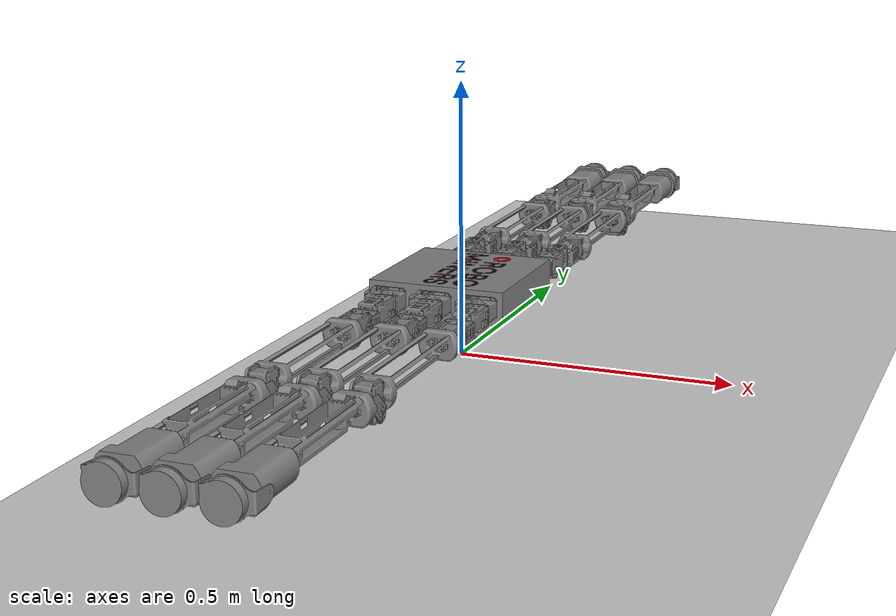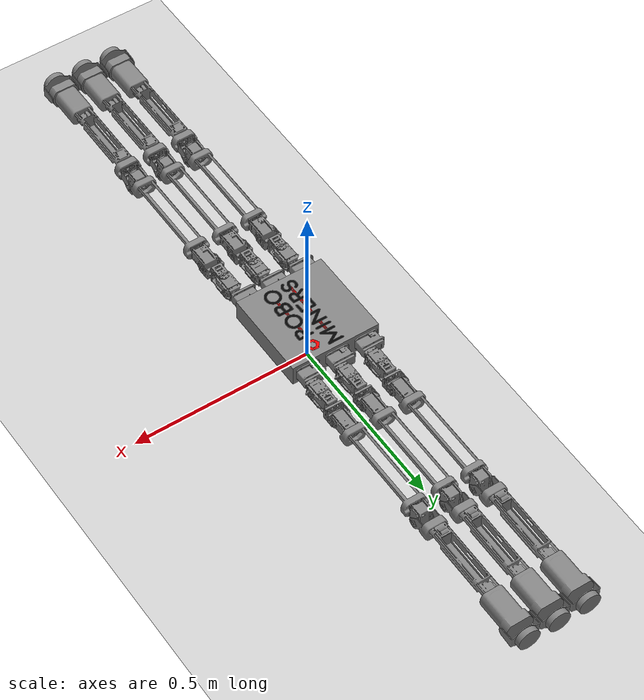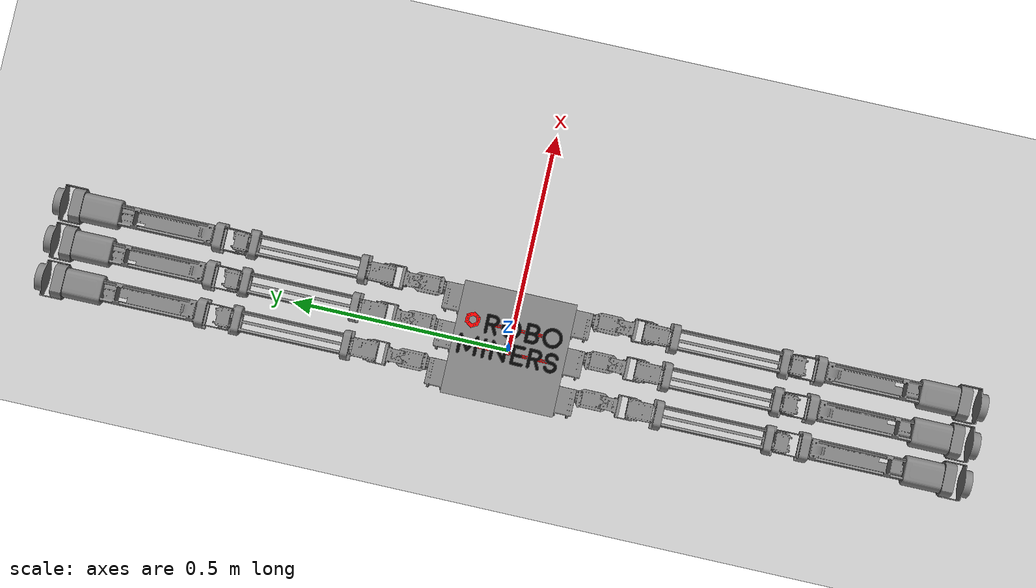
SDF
<?xml version="1.0" ?>
<sdf version="1.7">
    <world name="car_world">
        <physics name="1ms" type="ignored">
            <max_step_size>0.001</max_step_size>
            <real_time_factor>1.0</real_time_factor>
        </physics>
        <plugin
            filename="libignition-gazebo-physics-system.so"
            name="ignition::gazebo::systems::Physics">
        </plugin>
        <plugin
            filename="libignition-gazebo-user-commands-system.so"
            name="ignition::gazebo::systems::UserCommands">
        </plugin>
        <plugin
            filename="libignition-gazebo-scene-broadcaster-system.so"
            name="ignition::gazebo::systems::SceneBroadcaster">
        </plugin>

        <gui fullscreen="0">

            <!-- 3D scene -->
            <plugin filename="GzScene3D" name="3D View">
                <ignition-gui>
                <title>3D View</title>
                <property type="bool" key="showTitleBar">false</property>
                <property type="string" key="state">docked</property>
                </ignition-gui>

                <engine>ogre2</engine>
                <scene>scene</scene>
                <ambient_light>0.4 0.4 0.4</ambient_light>
                <background_color>0.8 0.8 0.8</background_color>
            </plugin>

            <!-- World control -->
            <plugin filename="WorldControl" name="World control">
                <ignition-gui>
                <title>World control</title>
                <property type="bool" key="showTitleBar">false</property>
                <property type="bool" key="resizable">false</property>
                <property type="double" key="height">72</property>
                <property type="double" key="width">121</property>
                <property type="double" key="z">1</property>

                <property type="string" key="state">floating</property>
                <anchors target="3D View">
                    <line own="left" target="left"/>
                    <line own="bottom" target="bottom"/>
                </anchors>
                </ignition-gui>

                <play_pause>true</play_pause>
                <step>true</step>
                <start_paused>true</start_paused>
                <service>/world/car_world/control</service>
                <stats_topic>/world/car_world/stats</stats_topic>
            </plugin>

            <!-- World statistics -->
            <plugin filename="WorldStats" name="World stats">
                <ignition-gui>
                <title>World stats</title>
                <property type="bool" key="showTitleBar">false</property>
                <property type="bool" key="resizable">false</property>
                <property type="double" key="height">110</property>
                <property type="double" key="width">290</property>
                <property type="double" key="z">1</property>

                <property type="string" key="state">floating</property>
                <anchors target="3D View">
                    <line own="right" target="right"/>
                    <line own="bottom" target="bottom"/>
                </anchors>
                </ignition-gui>

                <sim_time>true</sim_time>
                <real_time>true</real_time>
                <real_time_factor>true</real_time_factor>
                <iterations>true</iterations>
                <topic>/world/car_world/stats</topic>

            </plugin>

            <!-- Entity tree -->
            <plugin filename="EntityTree" name="Entity tree">
            </plugin>

            <!-- KeyPublisher plugin-->
            <plugin filename="KeyPublisher" name="Key Publisher"/>

        </gui>

        <light type="directional" name="sun">
            <cast_shadows>true</cast_shadows>
            <pose>0 0 10 0 0 0</pose>
            <diffuse>0.8 0.8 0.8 1</diffuse>
            <specular>0.2 0.2 0.2 1</specular>
            <attenuation>
                <range>1000</range>
                <constant>0.9</constant>
                <linear>0.01</linear>
                <quadratic>0.001</quadratic>
            </attenuation>
            <direction>-0.5 0.1 -0.9</direction>
        </light>

        <model name="ground_plane">
            <static>true</static>
            <link name="link">
                <collision name="collision">
                <geometry>
                    <plane>
                    <normal>0 0 1</normal>
                    </plane>
                </geometry>
                </collision>
                <visual name="visual">
                <geometry>
                    <plane>
                    <normal>0 0 1</normal>
                    <size>100 100</size>
                    </plane>
                </geometry>
                <material>
                    <ambient>0.8 0.8 0.8 1</ambient>
                    <diffuse>0.8 0.8 0.8 1</diffuse>
                    <specular>0.8 0.8 0.8 1</specular>
                </material>
                </visual>
            </link>
        </model>

	  <model name='robominer'>
	    <link name='base_link'>
	      <inertial>
	        <pose>0.003076 -0 0.129981 0 -0 0</pose>
 	        <mass>17.8454</mass>
  	      	<inertia>
 	         <ixx>0.394305</ixx>
        	 <ixy>-2.50112e-05</ixy>
          	 <ixz>4.11814e-06</ixz>
       	 <iyy>0.200825</iyy>
          	 <iyz>0.000548874</iyz>
          	 <izz>0.575646</izz>
              	</inertia>
      	      </inertial>
    	      <collision name='base_link_fixed_joint_lump__cuerpo_collision'>
        	<pose>0 0 0.1 0 -0 0</pose>
        	<geometry>
         	 <mesh>
          	  <scale>0.001 0.001 0.001</scale>
                 <uri>meshes/cuerpo.stl</uri>
                </mesh>
	        </geometry>
 	        <surface>
         	  <contact>
          	    <ode>
          	      <kp>1e+06</kp>
          	      <kd>1</kd>
     	  	      <max_vel>0</max_vel>
           	      <min_depth>0.001</min_depth>
         	    </ode>
         	  </contact>
      	         <friction>
           	 <ode>
             	   <mu>0.8</mu>
             	   <mu2>0.8</mu2>
          	 </ode>
                </friction>
      	        </surface>
      	       </collision>
      <collision name='base_link_fixed_joint_lump__Component1_l_1_collision_1'>
        <pose>0.100325 0.151 0.13 3.14159 -0 0</pose>
        <geometry>
          <mesh>
            <scale>0.001 0.001 0.001</scale>
            <uri>meshes/Component1_1.stl</uri>
          </mesh>
        </geometry>
        <surface>
          <contact>
            <ode>
              <kp>1e+06</kp>
              <kd>1</kd>
              <max_vel>0</max_vel>
              <min_depth>0.001</min_depth>
            </ode>
          </contact>
          <friction>
            <ode>
              <mu>0.8</mu>
              <mu2>0.8</mu2>
            </ode>
          </friction>
        </surface>
      </collision>
      <collision name='base_link_fixed_joint_lump__Component2_l_1_collision_2'>
        <pose>0.100395 0.151 0.12918 0 -0 3.14159</pose>
        <geometry>
          <mesh>
            <scale>0.001 0.001 0.001</scale>
            <uri>meshes/Component2_1.stl</uri>
          </mesh>
        </geometry>
        <surface>
          <contact>
            <ode>
              <kp>1e+06</kp>
              <kd>1</kd>
              <max_vel>0</max_vel>
              <min_depth>0.001</min_depth>
            </ode>
          </contact>
          <friction>
            <ode>
              <mu>0.8</mu>
              <mu2>0.8</mu2>
            </ode>
          </friction>
        </surface>
      </collision>
      <collision name='base_link_fixed_joint_lump__Component3_l_1_collision_3'>
        <pose>0.100395 0.151 0.12918 0 -0 3.14159</pose>
        <geometry>
          <mesh>
            <scale>0.001 0.001 0.001</scale>
            <uri>meshes/Component3_1.stl</uri>
          </mesh>
        </geometry>
        <surface>
          <contact>
            <ode>
              <kp>1e+06</kp>
              <kd>1</kd>
              <max_vel>0</max_vel>
              <min_depth>0.001</min_depth>
            </ode>
          </contact>
          <friction>
            <ode>
              <mu>0.8</mu>
              <mu2>0.8</mu2>
            </ode>
          </friction>
        </surface>
      </collision>
      <collision name='base_link_fixed_joint_lump__Component1_l_2_collision_4'>
        <pose>0.015325 0.151 0.13 3.14159 -0 0</pose>
        <geometry>
          <mesh>
            <scale>0.001 0.001 0.001</scale>
            <uri>meshes/Component1_1.stl</uri>
          </mesh>
        </geometry>
        <surface>
          <contact>
            <ode>
              <kp>1e+06</kp>
              <kd>1</kd>
              <max_vel>0</max_vel>
              <min_depth>0.001</min_depth>
            </ode>
          </contact>
          <friction>
            <ode>
              <mu>0.8</mu>
              <mu2>0.8</mu2>
            </ode>
          </friction>
        </surface>
      </collision>
      <collision name='base_link_fixed_joint_lump__Component2_l_2_collision_5'>
        <pose>0.015395 0.151 0.12918 0 -0 3.14159</pose>
        <geometry>
          <mesh>
            <scale>0.001 0.001 0.001</scale>
            <uri>meshes/Component2_1.stl</uri>
          </mesh>
        </geometry>
        <surface>
          <contact>
            <ode>
              <kp>1e+06</kp>
              <kd>1</kd>
              <max_vel>0</max_vel>
              <min_depth>0.001</min_depth>
            </ode>
          </contact>
          <friction>
            <ode>
              <mu>0.8</mu>
              <mu2>0.8</mu2>
            </ode>
          </friction>
        </surface>
      </collision>
      <collision name='base_link_fixed_joint_lump__Component3_l_2_collision_6'>
        <pose>0.015395 0.151 0.12918 0 -0 3.14159</pose>
        <geometry>
          <mesh>
            <scale>0.001 0.001 0.001</scale>
            <uri>meshes/Component3_1.stl</uri>
          </mesh>
        </geometry>
        <surface>
          <contact>
            <ode>
              <kp>1e+06</kp>
              <kd>1</kd>
              <max_vel>0</max_vel>
              <min_depth>0.001</min_depth>
            </ode>
          </contact>
          <friction>
            <ode>
              <mu>0.8</mu>
              <mu2>0.8</mu2>
            </ode>
          </friction>
        </surface>
      </collision>
      <collision name='base_link_fixed_joint_lump__Component1_l_3_collision_7'>
        <pose>-0.069675 0.151 0.13 3.14159 -0 0</pose>
        <geometry>
          <mesh>
            <scale>0.001 0.001 0.001</scale>
            <uri>meshes/Component1_1.stl</uri>
          </mesh>
        </geometry>
        <surface>
          <contact>
            <ode>
              <kp>1e+06</kp>
              <kd>1</kd>
              <max_vel>0</max_vel>
              <min_depth>0.001</min_depth>
            </ode>
          </contact>
          <friction>
            <ode>
              <mu>0.8</mu>
              <mu2>0.8</mu2>
            </ode>
          </friction>
        </surface>
      </collision>
      <collision name='base_link_fixed_joint_lump__Component2_l_3_collision_8'>
        <pose>-0.069605 0.151 0.12918 0 -0 3.14159</pose>
        <geometry>
          <mesh>
            <scale>0.001 0.001 0.001</scale>
            <uri>meshes/Component2_1.stl</uri>
          </mesh>
        </geometry>
        <surface>
          <contact>
            <ode>
              <kp>1e+06</kp>
              <kd>1</kd>
              <max_vel>0</max_vel>
              <min_depth>0.001</min_depth>
            </ode>
          </contact>
          <friction>
            <ode>
              <mu>0.8</mu>
              <mu2>0.8</mu2>
            </ode>
          </friction>
        </surface>
      </collision>
      <collision name='base_link_fixed_joint_lump__Component3_l_3_collision_9'>
        <pose>-0.069605 0.151 0.12918 0 -0 3.14159</pose>
        <geometry>
          <mesh>
            <scale>0.001 0.001 0.001</scale>
            <uri>meshes/Component3_1.stl</uri>
          </mesh>
        </geometry>
        <surface>
          <contact>
            <ode>
              <kp>1e+06</kp>
              <kd>1</kd>
              <max_vel>0</max_vel>
              <min_depth>0.001</min_depth>
            </ode>
          </contact>
          <friction>
            <ode>
              <mu>0.8</mu>
              <mu2>0.8</mu2>
            </ode>
          </friction>
        </surface>
      </collision>
      <collision name='base_link_fixed_joint_lump__Component1_r_1_collision_10'>
        <pose>0.100325 -0.151 0.13 0 -0 0</pose>
        <geometry>
          <mesh>
            <scale>0.001 0.001 0.001</scale>
            <uri>meshes/Component1_1.stl</uri>
          </mesh>
        </geometry>
        <surface>
          <contact>
            <ode>
              <kp>1e+06</kp>
              <kd>1</kd>
              <max_vel>0</max_vel>
              <min_depth>0.001</min_depth>
            </ode>
          </contact>
          <friction>
            <ode>
              <mu>0.8</mu>
              <mu2>0.8</mu2>
            </ode>
          </friction>
        </surface>
      </collision>
      <collision name='base_link_fixed_joint_lump__Component2_r_1_collision_11'>
        <pose>0.100325 -0.151 0.13 0 -0 0</pose>
        <geometry>
          <mesh>
            <scale>0.001 0.001 0.001</scale>
            <uri>meshes/Component2_1.stl</uri>
          </mesh>
        </geometry>
        <surface>
          <contact>
            <ode>
              <kp>1e+06</kp>
              <kd>1</kd>
              <max_vel>0</max_vel>
              <min_depth>0.001</min_depth>
            </ode>
          </contact>
          <friction>
            <ode>
              <mu>0.8</mu>
              <mu2>0.8</mu2>
            </ode>
          </friction>
        </surface>
      </collision>
      <collision name='base_link_fixed_joint_lump__Component3_r_1_collision_12'>
        <pose>0.100325 -0.151 0.13 0 -0 0</pose>
        <geometry>
          <mesh>
            <scale>0.001 0.001 0.001</scale>
            <uri>meshes/Component3_1.stl</uri>
          </mesh>
        </geometry>
        <surface>
          <contact>
            <ode>
              <kp>1e+06</kp>
              <kd>1</kd>
              <max_vel>0</max_vel>
              <min_depth>0.001</min_depth>
            </ode>
          </contact>
          <friction>
            <ode>
              <mu>0.8</mu>
              <mu2>0.8</mu2>
            </ode>
          </friction>
        </surface>
      </collision>
      <collision name='base_link_fixed_joint_lump__Component1_r_2_collision_13'>
        <pose>0.015325 -0.151 0.13 0 -0 0</pose>
        <geometry>
          <mesh>
            <scale>0.001 0.001 0.001</scale>
            <uri>meshes/Component1_1.stl</uri>
          </mesh>
        </geometry>
        <surface>
          <contact>
            <ode>
              <kp>1e+06</kp>
              <kd>1</kd>
              <max_vel>0</max_vel>
              <min_depth>0.001</min_depth>
            </ode>
          </contact>
          <friction>
            <ode>
              <mu>0.8</mu>
              <mu2>0.8</mu2>
            </ode>
          </friction>
        </surface>
      </collision>
      <collision name='base_link_fixed_joint_lump__Component2_r_2_collision_14'>
        <pose>0.015325 -0.151 0.13 0 -0 0</pose>
        <geometry>
          <mesh>
            <scale>0.001 0.001 0.001</scale>
            <uri>meshes/Component2_1.stl</uri>
          </mesh>
        </geometry>
        <surface>
          <contact>
            <ode>
              <kp>1e+06</kp>
              <kd>1</kd>
              <max_vel>0</max_vel>
              <min_depth>0.001</min_depth>
            </ode>
          </contact>
          <friction>
            <ode>
              <mu>0.8</mu>
              <mu2>0.8</mu2>
            </ode>
          </friction>
        </surface>
      </collision>
      <collision name='base_link_fixed_joint_lump__Component3_r_2_collision_15'>
        <pose>0.015325 -0.151 0.13 0 -0 0</pose>
        <geometry>
          <mesh>
            <scale>0.001 0.001 0.001</scale>
            <uri>meshes/Component3_1.stl</uri>
          </mesh>
        </geometry>
        <surface>
          <contact>
            <ode>
              <kp>1e+06</kp>
              <kd>1</kd>
              <max_vel>0</max_vel>
              <min_depth>0.001</min_depth>
            </ode>
          </contact>
          <friction>
            <ode>
              <mu>0.8</mu>
              <mu2>0.8</mu2>
            </ode>
          </friction>
        </surface>
      </collision>
      <collision name='base_link_fixed_joint_lump__Component1_r_3_collision_16'>
        <pose>-0.069675 -0.151 0.13 0 -0 0</pose>
        <geometry>
          <mesh>
            <scale>0.001 0.001 0.001</scale>
            <uri>meshes/Component1_1.stl</uri>
          </mesh>
        </geometry>
        <surface>
          <contact>
            <ode>
              <kp>1e+06</kp>
              <kd>1</kd>
              <max_vel>0</max_vel>
              <min_depth>0.001</min_depth>
            </ode>
          </contact>
          <friction>
            <ode>
              <mu>0.8</mu>
              <mu2>0.8</mu2>
            </ode>
          </friction>
        </surface>
      </collision>
      <collision name='base_link_fixed_joint_lump__Component2_r_3_collision_17'>
        <pose>-0.069675 -0.151 0.13 0 -0 0</pose>
        <geometry>
          <mesh>
            <scale>0.001 0.001 0.001</scale>
            <uri>meshes/Component2_1.stl</uri>
          </mesh>
        </geometry>
        <surface>
          <contact>
            <ode>
              <kp>1e+06</kp>
              <kd>1</kd>
              <max_vel>0</max_vel>
              <min_depth>0.001</min_depth>
            </ode>
          </contact>
          <friction>
            <ode>
              <mu>0.8</mu>
              <mu2>0.8</mu2>
            </ode>
          </friction>
        </surface>
      </collision>
      <collision name='base_link_fixed_joint_lump__Component3_r_3_collision_18'>
        <pose>-0.069675 -0.151 0.13 0 -0 0</pose>
        <geometry>
          <mesh>
            <scale>0.001 0.001 0.001</scale>
            <uri>meshes/Component3_1.stl</uri>
          </mesh>
        </geometry>
        <surface>
          <contact>
            <ode>
              <kp>1e+06</kp>
              <kd>1</kd>
              <max_vel>0</max_vel>
              <min_depth>0.001</min_depth>
            </ode>
          </contact>
          <friction>
            <ode>
              <mu>0.8</mu>
              <mu2>0.8</mu2>
            </ode>
          </friction>
        </surface>
      </collision>
      <visual name='base_link_fixed_joint_lump__cuerpo_visual'>
        <pose>0 0 0.1 0 -0 0</pose>
        <geometry>
          <mesh>
            <scale>0.001 0.001 0.001</scale>
            <uri>meshes/cuerpo.stl</uri>
          </mesh>
        </geometry>
        <material>
	  <ambient>0.19225 0.19225 0.19225 1</ambient>
  	  <diffuse>0.50754 0.50754 0.50754 1</diffuse>
  	  <specular>0.508273 0.508273 0.508273 1</specular>
        </material>
      </visual>
      <visual name='base_link_fixed_joint_lump__Component1_l_1_visual_1'>
        <pose>0.100325 0.151 0.13 3.14159 -0 0</pose>
        <geometry>
          <mesh>
            <scale>0.001 0.001 0.001</scale>
            <uri>meshes/Component1_1.stl</uri>
          </mesh>
        </geometry>
        <material>
	  <ambient>0.19225 0.19225 0.19225 1</ambient>
  	  <diffuse>0.50754 0.50754 0.50754 1</diffuse>
  	  <specular>0.508273 0.508273 0.508273 1</specular>
        </material>
      </visual>
      <visual name='base_link_fixed_joint_lump__Component2_l_1_visual_2'>
        <pose>0.100395 0.151 0.12918 0 -0 3.14159</pose>
        <geometry>
          <mesh>
            <scale>0.001 0.001 0.001</scale>
            <uri>meshes/Component2_1.stl</uri>
          </mesh>
        </geometry>
        <material>
	  <ambient>0.19225 0.19225 0.19225 1</ambient>
  	  <diffuse>0.50754 0.50754 0.50754 1</diffuse>
  	  <specular>0.508273 0.508273 0.508273 1</specular>
        </material>
      </visual>
      <visual name='base_link_fixed_joint_lump__Component3_l_1_visual_3'>
        <pose>0.100395 0.151 0.12918 0 -0 3.14159</pose>
        <geometry>
          <mesh>
            <scale>0.001 0.001 0.001</scale>
            <uri>meshes/Component3_1.stl</uri>
          </mesh>
        </geometry>
        <material>
	  <ambient>0.19225 0.19225 0.19225 1</ambient>
  	  <diffuse>0.50754 0.50754 0.50754 1</diffuse>
  	  <specular>0.508273 0.508273 0.508273 1</specular>
        </material>
      </visual>
      <visual name='base_link_fixed_joint_lump__Component1_l_2_visual_4'>
        <pose>0.015325 0.151 0.13 3.14159 -0 0</pose>
        <geometry>
          <mesh>
            <scale>0.001 0.001 0.001</scale>
            <uri>meshes/Component1_1.stl</uri>
          </mesh>
        </geometry>
        <material>
	  <ambient>0.19225 0.19225 0.19225 1</ambient>
  	  <diffuse>0.50754 0.50754 0.50754 1</diffuse>
  	  <specular>0.508273 0.508273 0.508273 1</specular>
        </material>
      </visual>
      <visual name='base_link_fixed_joint_lump__Component2_l_2_visual_5'>
        <pose>0.015395 0.151 0.12918 0 -0 3.14159</pose>
        <geometry>
          <mesh>
            <scale>0.001 0.001 0.001</scale>
            <uri>meshes/Component2_1.stl</uri>
          </mesh>
        </geometry>
        <material>
	  <ambient>0.19225 0.19225 0.19225 1</ambient>
  	  <diffuse>0.50754 0.50754 0.50754 1</diffuse>
  	  <specular>0.508273 0.508273 0.508273 1</specular>
        </material>
      </visual>
      <visual name='base_link_fixed_joint_lump__Component3_l_2_visual_6'>
        <pose>0.015395 0.151 0.12918 0 -0 3.14159</pose>
        <geometry>
          <mesh>
            <scale>0.001 0.001 0.001</scale>
            <uri>meshes/Component3_1.stl</uri>
          </mesh>
        </geometry>
        <material>
	  <ambient>0.19225 0.19225 0.19225 1</ambient>
  	  <diffuse>0.50754 0.50754 0.50754 1</diffuse>
  	  <specular>0.508273 0.508273 0.508273 1</specular>
        </material>
      </visual>
      <visual name='base_link_fixed_joint_lump__Component1_l_3_visual_7'>
        <pose>-0.069675 0.151 0.13 3.14159 -0 0</pose>
        <geometry>
          <mesh>
            <scale>0.001 0.001 0.001</scale>
            <uri>meshes/Component1_1.stl</uri>
          </mesh>
        </geometry>
        <material>
	  <ambient>0.19225 0.19225 0.19225 1</ambient>
  	  <diffuse>0.50754 0.50754 0.50754 1</diffuse>
  	  <specular>0.508273 0.508273 0.508273 1</specular>
        </material>
      </visual>
      <visual name='base_link_fixed_joint_lump__Component2_l_3_visual_8'>
        <pose>-0.069605 0.151 0.12918 0 -0 3.14159</pose>
        <geometry>
          <mesh>
            <scale>0.001 0.001 0.001</scale>
            <uri>meshes/Component2_1.stl</uri>
          </mesh>
        </geometry>
        <material>
	  <ambient>0.19225 0.19225 0.19225 1</ambient>
  	  <diffuse>0.50754 0.50754 0.50754 1</diffuse>
  	  <specular>0.508273 0.508273 0.508273 1</specular>
        </material>
      </visual>
      <visual name='base_link_fixed_joint_lump__Component3_l_3_visual_9'>
        <pose>-0.069605 0.151 0.12918 0 -0 3.14159</pose>
        <geometry>
          <mesh>
            <scale>0.001 0.001 0.001</scale>
            <uri>meshes/Component3_1.stl</uri>
          </mesh>
        </geometry>
        <material>
	  <ambient>0.19225 0.19225 0.19225 1</ambient>
  	  <diffuse>0.50754 0.50754 0.50754 1</diffuse>
  	  <specular>0.508273 0.508273 0.508273 1</specular>
        </material>
      </visual>
      <visual name='base_link_fixed_joint_lump__Component1_r_1_visual_10'>
        <pose>0.100325 -0.151 0.13 0 -0 0</pose>
        <geometry>
          <mesh>
            <scale>0.001 0.001 0.001</scale>
            <uri>meshes/Component1_1.stl</uri>
          </mesh>
        </geometry>
        <material>
	  <ambient>0.19225 0.19225 0.19225 1</ambient>
  	  <diffuse>0.50754 0.50754 0.50754 1</diffuse>
  	  <specular>0.508273 0.508273 0.508273 1</specular>
        </material>
      </visual>
      <visual name='base_link_fixed_joint_lump__Component2_r_1_visual_11'>
        <pose>0.100325 -0.151 0.13 0 -0 0</pose>
        <geometry>
          <mesh>
            <scale>0.001 0.001 0.001</scale>
            <uri>meshes/Component2_1.stl</uri>
          </mesh>
        </geometry>
        <material>
	  <ambient>0.19225 0.19225 0.19225 1</ambient>
  	  <diffuse>0.50754 0.50754 0.50754 1</diffuse>
  	  <specular>0.508273 0.508273 0.508273 1</specular>
        </material>
      </visual>
      <visual name='base_link_fixed_joint_lump__Component3_r_1_visual_12'>
        <pose>0.100325 -0.151 0.13 0 -0 0</pose>
        <geometry>
          <mesh>
            <scale>0.001 0.001 0.001</scale>
            <uri>meshes/Component3_1.stl</uri>
          </mesh>
        </geometry>
        <material>
	  <ambient>0.19225 0.19225 0.19225 1</ambient>
  	  <diffuse>0.50754 0.50754 0.50754 1</diffuse>
  	  <specular>0.508273 0.508273 0.508273 1</specular>
        </material>
      </visual>
      <visual name='base_link_fixed_joint_lump__Component1_r_2_visual_13'>
        <pose>0.015325 -0.151 0.13 0 -0 0</pose>
        <geometry>
          <mesh>
            <scale>0.001 0.001 0.001</scale>
            <uri>meshes/Component1_1.stl</uri>
          </mesh>
        </geometry>
        <material>
	  <ambient>0.19225 0.19225 0.19225 1</ambient>
  	  <diffuse>0.50754 0.50754 0.50754 1</diffuse>
  	  <specular>0.508273 0.508273 0.508273 1</specular>
        </material>
      </visual>
      <visual name='base_link_fixed_joint_lump__Component2_r_2_visual_14'>
        <pose>0.015325 -0.151 0.13 0 -0 0</pose>
        <geometry>
          <mesh>
            <scale>0.001 0.001 0.001</scale>
            <uri>meshes/Component2_1.stl</uri>
          </mesh>
        </geometry>
        <material>
	  <ambient>0.19225 0.19225 0.19225 1</ambient>
  	  <diffuse>0.50754 0.50754 0.50754 1</diffuse>
  	  <specular>0.508273 0.508273 0.508273 1</specular>
        </material>
      </visual>
      <visual name='base_link_fixed_joint_lump__Component3_r_2_visual_15'>
        <pose>0.015325 -0.151 0.13 0 -0 0</pose>
        <geometry>
          <mesh>
            <scale>0.001 0.001 0.001</scale>
            <uri>meshes/Component3_1.stl</uri>
          </mesh>
        </geometry>
        <material>
	  <ambient>0.19225 0.19225 0.19225 1</ambient>
  	  <diffuse>0.50754 0.50754 0.50754 1</diffuse>
  	  <specular>0.508273 0.508273 0.508273 1</specular>
        </material>
      </visual>
      <visual name='base_link_fixed_joint_lump__Component1_r_3_visual_16'>
        <pose>-0.069675 -0.151 0.13 0 -0 0</pose>
        <geometry>
          <mesh>
            <scale>0.001 0.001 0.001</scale>
            <uri>meshes/Component1_1.stl</uri>
          </mesh>
        </geometry>
        <material>
	  <ambient>0.19225 0.19225 0.19225 1</ambient>
  	  <diffuse>0.50754 0.50754 0.50754 1</diffuse>
  	  <specular>0.508273 0.508273 0.508273 1</specular>
        </material>
      </visual>
      <visual name='base_link_fixed_joint_lump__Component2_r_3_visual_17'>
        <pose>-0.069675 -0.151 0.13 0 -0 0</pose>
        <geometry>
          <mesh>
            <scale>0.001 0.001 0.001</scale>
            <uri>meshes/Component2_1.stl</uri>
          </mesh>
        </geometry>
        <material>
	  <ambient>0.19225 0.19225 0.19225 1</ambient>
  	  <diffuse>0.50754 0.50754 0.50754 1</diffuse>
  	  <specular>0.508273 0.508273 0.508273 1</specular>
        </material>
      </visual>
      <visual name='base_link_fixed_joint_lump__Component3_r_3_visual_18'>
        <pose>-0.069675 -0.151 0.13 0 -0 0</pose>
        <geometry>
          <mesh>
            <scale>0.001 0.001 0.001</scale>
            <uri>meshes/Component3_1.stl</uri>
          </mesh>
        </geometry>
        <material>
	  <ambient>0.19225 0.19225 0.19225 1</ambient>
  	  <diffuse>0.50754 0.50754 0.50754 1</diffuse>
  	  <specular>0.508273 0.508273 0.508273 1</specular>
        </material>
      </visual>
      <visual name='base_link_fixed_joint_lump__ladrilloslogo_visual_19'>
        <pose>0.08 0.125 0.1551 0 0 -1.5707</pose>
        <geometry>
          <mesh>
            <scale>0.001 0.001 0.001</scale>
            <uri>meshes/ladrilloslogo.stl</uri>
          </mesh>
        </geometry>
        <material>
	  <ambient>1 0 0 1</ambient>
  	  <diffuse>1 0 0 1</diffuse>
  	  <specular>0.1 0.1 0.1 1</specular>
        </material>
      </visual>
      <visual name='base_link_fixed_joint_lump__logo1_visual_20'>
        <pose>-0.006 0.105 0.1551 0 -0 0.5236</pose>
        <geometry>
          <mesh>
            <scale>0.001 0.001 0.001</scale>
            <uri>meshes/logo1.stl</uri>
          </mesh>
        </geometry>
        <material>
	  <ambient>1 0 0 1</ambient>
  	  <diffuse>1 0 0 1</diffuse>
  	  <specular>0.1 0.1 0.1 1</specular>
        </material>
      </visual>
      <visual name='base_link_fixed_joint_lump__logo2_visual_21'>
        <pose>0.08 0.125 0.1552 0 0 -1.5707</pose>
        <geometry>
          <mesh>
            <scale>0.001 0.001 0.001</scale>
            <uri>meshes/logo2.stl</uri>
          </mesh>
        </geometry>
        <material>
	  <ambient>0 0 0 1</ambient>
  	  <diffuse>0.01 0.01 0.01 1</diffuse>
  	  <specular>0.5 0.5 0.5 1</specular>
        </material>
      </visual>
      <velocity_decay/>
      <velocity_decay/>
      <velocity_decay/>
      <velocity_decay/>
      <velocity_decay/>
      <velocity_decay/>
      <velocity_decay/>
      <velocity_decay/>
      <velocity_decay/>
      <velocity_decay/>
      <velocity_decay/>
      <velocity_decay/>
      <velocity_decay/>
      <velocity_decay/>
      <velocity_decay/>
      <velocity_decay/>
      <velocity_decay/>
      <velocity_decay/>
      <velocity_decay/>
      <velocity_decay/>
      <gravity>1</gravity>
      <velocity_decay/>
      <gravity>1</gravity>
      <velocity_decay/>
      <self_collide>1</self_collide>
    </link>
    <joint name='Rev3_l_1' type='revolute'>
      <pose relative_to='base_link'>0.10036 0.220279 0.153079 0 -0 3.14159</pose>
      <parent>base_link</parent>
      <child>Component4_l_1</child>
      <axis>
        <xyz>0 0 1</xyz>
        <limit>
          <lower>-1.91986</lower>
          <upper>1.91986</upper>
          <effort>100</effort>
          <velocity>0.75</velocity>
        </limit>
        <dynamics>
          <damping>0.1</damping>
          <friction>1</friction>
          <spring_reference>0</spring_reference>
          <spring_stiffness>0</spring_stiffness>
        </dynamics>
      </axis>
      <physics>
        <provide_feedback>1</provide_feedback>
        <ode>
          <limit>
            <cfm>0</cfm>
            <erp>0.2</erp>
          </limit>
          <provide_feedback>1</provide_feedback>
        </ode>
      </physics>
    </joint>
    <link name='Component4_l_1'>
      <pose relative_to='Rev3_l_1'>0 0 0 0 -0 0</pose>
      <inertial>
        <pose>0 -0.036 -0.0235 0 -0 0</pose>
        <mass>0.104168</mass>
        <inertia>
          <ixx>5.11669e-05</ixx>
          <ixy>1.40991e-12</ixy>
          <ixz>7.2465e-20</ixz>
          <iyy>5.2e-05</iyy>
          <iyz>-5.73941e-13</iyz>
          <izz>5.11669e-05</izz>
        </inertia>
      </inertial>
      <collision name='Component4_l_1_collision'>
        <pose>-3.5e-05 0.069279 -0.023899 0 -0 0</pose>
        <geometry>
          <mesh>
            <scale>0.001 0.001 0.001</scale>
            <uri>meshes/Component4_1.stl</uri>
          </mesh>
        </geometry>
        <surface>
          <contact>
            <ode>
              <kp>1e+06</kp>
              <kd>1</kd>
              <max_vel>0</max_vel>
              <min_depth>0.001</min_depth>
            </ode>
          </contact>
          <friction>
            <ode>
              <mu>0.8</mu>
              <mu2>0.8</mu2>
            </ode>
          </friction>
        </surface>
      </collision>
      <collision name='Component4_l_1_fixed_joint_lump__Component5_l_1_collision_1'>
        <pose>-3.5e-05 0.069279 -0.023899 0 -0 0</pose>
        <geometry>
          <mesh>
            <scale>0.001 0.001 0.001</scale>
            <uri>meshes/Component5_1.stl</uri>
          </mesh>
        </geometry>
        <surface>
          <contact>
            <ode>
              <kp>1e+06</kp>
              <kd>1</kd>
              <max_vel>0</max_vel>
              <min_depth>0.001</min_depth>
            </ode>
          </contact>
          <friction>
            <ode>
              <mu>0.8</mu>
              <mu2>0.8</mu2>
            </ode>
          </friction>
        </surface>
      </collision>
      <visual name='Component4_l_1_visual'>
        <pose>-3.5e-05 0.069279 -0.023899 0 -0 0</pose>
        <geometry>
          <mesh>
            <scale>0.001 0.001 0.001</scale>
            <uri>meshes/Component4_1.stl</uri>
          </mesh>
        </geometry>
        <material>
	  <ambient>0.19225 0.19225 0.19225 1</ambient>
  	  <diffuse>0.50754 0.50754 0.50754 1</diffuse>
  	  <specular>0.508273 0.508273 0.508273 1</specular>
        </material>
      </visual>
      <visual name='Component4_l_1_fixed_joint_lump__Component5_l_1_visual_1'>
        <pose>-3.5e-05 0.069279 -0.023899 0 -0 0</pose>
        <geometry>
          <mesh>
            <scale>0.001 0.001 0.001</scale>
            <uri>meshes/Component5_1.stl</uri>
          </mesh>
        </geometry>
        <material>
	  <ambient>0.19225 0.19225 0.19225 1</ambient>
  	  <diffuse>0.50754 0.50754 0.50754 1</diffuse>
  	  <specular>0.508273 0.508273 0.508273 1</specular>
        </material>
      </visual>
      <velocity_decay/>
      <gravity>1</gravity>
      <velocity_decay/>
      <self_collide>1</self_collide>
    </link>
    <joint name='Rev5_l_1' type='revolute'>
      <pose relative_to='Component4_l_1'>0.0235 -0.072 -0.0235 0 -0 0</pose>
      <parent>Component4_l_1</parent>
      <child>Component6_l_1</child>
      <axis>
        <xyz>1 0 0</xyz>
        <limit>
          <lower>-1.91986</lower>
          <upper>1.91986</upper>
          <effort>100</effort>
          <velocity>0.75</velocity>
        </limit>
        <dynamics>
          <damping>0.1</damping>
          <friction>1</friction>
          <spring_reference>0</spring_reference>
          <spring_stiffness>0</spring_stiffness>
        </dynamics>
      </axis>
      <physics>
        <provide_feedback>1</provide_feedback>
        <ode>
          <limit>
            <cfm>0</cfm>
            <erp>0.2</erp>
          </limit>
          <provide_feedback>1</provide_feedback>
        </ode>
      </physics>
    </joint>
    <link name='Component6_l_1'>
      <pose relative_to='Rev5_l_1'>0 0 0 0 -0 0</pose>
      <inertial>
        <pose>-0.023547 -0.175176 -0.001507 0 -0 0</pose>
        <mass>1.98279</mass>
        <inertia>
          <ixx>0.0398853</ixx>
          <ixy>-9.86615e-07</ixy>
          <ixz>2.90065e-06</ixz>
          <iyy>0.000870749</iyy>
          <iyz>-0.000622888</iyz>
          <izz>0.0399515</izz>
        </inertia>
      </inertial>
      <collision name='Component6_l_1_collision'>
        <pose>-0.023535 0.141279 -0.000399 0 -0 0</pose>
        <geometry>
          <mesh>
            <scale>0.001 0.001 0.001</scale>
            <uri>meshes/Component6_1.stl</uri>
          </mesh>
        </geometry>
        <surface>
          <contact>
            <ode>
              <kp>1e+06</kp>
              <kd>1</kd>
              <max_vel>0</max_vel>
              <min_depth>0.001</min_depth>
            </ode>
          </contact>
          <friction>
            <ode>
              <mu>0.8</mu>
              <mu2>0.8</mu2>
            </ode>
          </friction>
        </surface>
      </collision>
      <collision name='Component6_l_1_fixed_joint_lump__Component7_l_1_collision_1'>
        <pose>-0.023535 0.141279 -0.000399 0 -0 0</pose>
        <geometry>
          <mesh>
            <scale>0.001 0.001 0.001</scale>
            <uri>meshes/Component7_1.stl</uri>
          </mesh>
        </geometry>
        <surface>
          <contact>
            <ode>
              <kp>1e+06</kp>
              <kd>1</kd>
              <max_vel>0</max_vel>
              <min_depth>0.001</min_depth>
            </ode>
          </contact>
          <friction>
            <ode>
              <mu>0.8</mu>
              <mu2>0.8</mu2>
            </ode>
          </friction>
        </surface>
      </collision>
      <collision name='Component6_l_1_fixed_joint_lump__Component8_l_1_collision_2'>
        <pose>-0.023535 0.141279 -0.000399 0 -0 0</pose>
        <geometry>
          <mesh>
            <scale>0.001 0.001 0.001</scale>
            <uri>meshes/Component8_1.stl</uri>
          </mesh>
        </geometry>
        <surface>
          <contact>
            <ode>
              <kp>1e+06</kp>
              <kd>1</kd>
              <max_vel>0</max_vel>
              <min_depth>0.001</min_depth>
            </ode>
          </contact>
          <friction>
            <ode>
              <mu>0.8</mu>
              <mu2>0.8</mu2>
            </ode>
          </friction>
        </surface>
      </collision>
      <visual name='Component6_l_1_visual'>
        <pose>-0.023535 0.141279 -0.000399 0 -0 0</pose>
        <geometry>
          <mesh>
            <scale>0.001 0.001 0.001</scale>
            <uri>meshes/Component6_1.stl</uri>
          </mesh>
        </geometry>
        <material>
	  <ambient>0.19225 0.19225 0.19225 1</ambient>
  	  <diffuse>0.50754 0.50754 0.50754 1</diffuse>
  	  <specular>0.508273 0.508273 0.508273 1</specular>
        </material>
      </visual>
      <visual name='Component6_l_1_fixed_joint_lump__Component7_l_1_visual_1'>
        <pose>-0.023535 0.141279 -0.000399 0 -0 0</pose>
        <geometry>
          <mesh>
            <scale>0.001 0.001 0.001</scale>
            <uri>meshes/Component7_1.stl</uri>
          </mesh>
        </geometry>
        <material>
	  <ambient>0.19225 0.19225 0.19225 1</ambient>
  	  <diffuse>0.50754 0.50754 0.50754 1</diffuse>
  	  <specular>0.508273 0.508273 0.508273 1</specular>
        </material>
      </visual>
      <visual name='Component6_l_1_fixed_joint_lump__Component8_l_1_visual_2'>
        <pose>-0.023535 0.141279 -0.000399 0 -0 0</pose>
        <geometry>
          <mesh>
            <scale>0.001 0.001 0.001</scale>
            <uri>meshes/Component8_1.stl</uri>
          </mesh>
        </geometry>
        <material>
	  <ambient>0.19225 0.19225 0.19225 1</ambient>
  	  <diffuse>0.50754 0.50754 0.50754 1</diffuse>
  	  <specular>0.508273 0.508273 0.508273 1</specular>
        </material>
      </visual>
      <velocity_decay/>
      <velocity_decay/>
      <gravity>1</gravity>
      <velocity_decay/>
      <self_collide>1</self_collide>
    </link>
    <joint name='Rev8_l_1' type='revolute'>
      <pose relative_to='Component6_l_1'>-0.045522 -0.33 -0.022 0 -0 0</pose>
      <parent>Component6_l_1</parent>
      <child>Component9_l_1</child>
      <axis>
        <xyz>1 0 0</xyz>
        <limit>
          <lower>-0.785398</lower>
          <upper>3.14159</upper>
          <effort>100</effort>
          <velocity>0.75</velocity>
        </limit>
        <dynamics>
          <damping>0.1</damping>
          <friction>1</friction>
          <spring_reference>0</spring_reference>
          <spring_stiffness>0</spring_stiffness>
        </dynamics>
      </axis>
      <physics>
        <provide_feedback>1</provide_feedback>
        <ode>
          <limit>
            <cfm>0</cfm>
            <erp>0.2</erp>
          </limit>
          <provide_feedback>1</provide_feedback>
        </ode>
      </physics>
    </joint>
    <link name='Component9_l_1'>
      <pose relative_to='Rev8_l_1'>0 0 0 0 -0 0</pose>
      <inertial>
        <pose>0.023408 -0.266466 0.022962 0 -0 0</pose>
        <mass>3.75407</mass>
        <inertia>
          <ixx>0.045571</ixx>
          <ixy>-9.18481e-06</ixy>
          <ixz>2.13404e-07</ixz>
          <iyy>0.00185876</iyy>
          <iyz>-0.000505752</iyz>
          <izz>0.0459553</izz>
        </inertia>
      </inertial>
      <collision name='Component9_l_1_collision'>
        <pose>0.021987 0.471279 0.021601 0 -0 0</pose>
        <geometry>
          <mesh>
            <scale>0.001 0.001 0.001</scale>
            <uri>meshes/Component9_1.stl</uri>
          </mesh>
        </geometry>
        <surface>
          <contact>
            <ode>
              <kp>1e+06</kp>
              <kd>1</kd>
              <max_vel>0</max_vel>
              <min_depth>0.001</min_depth>
            </ode>
          </contact>
          <friction>
            <ode>
              <mu>0.8</mu>
              <mu2>0.8</mu2>
            </ode>
          </friction>
        </surface>
      </collision>
      <collision name='Component9_l_1_fixed_joint_lump__Component10_l_1_collision_1'>
        <pose>0.021987 0.471279 0.021601 0 -0 0</pose>
        <geometry>
          <mesh>
            <scale>0.001 0.001 0.001</scale>
            <uri>meshes/Component10_1.stl</uri>
          </mesh>
        </geometry>
        <surface>
          <contact>
            <ode>
              <kp>1e+06</kp>
              <kd>1</kd>
              <max_vel>0</max_vel>
              <min_depth>0.001</min_depth>
            </ode>
          </contact>
          <friction>
            <ode>
              <mu>0.8</mu>
              <mu2>0.8</mu2>
            </ode>
          </friction>
        </surface>
      </collision>
      <collision name='Component9_l_1_fixed_joint_lump__Component11_l_1_collision_2'>
        <pose>0.021987 0.471279 0.021601 0 -0 0</pose>
        <geometry>
          <mesh>
            <scale>0.001 0.001 0.001</scale>
            <uri>meshes/Component11_1.stl</uri>
          </mesh>
        </geometry>
        <surface>
          <contact>
            <ode>
              <kp>1e+06</kp>
              <kd>1</kd>
              <max_vel>0</max_vel>
              <min_depth>0.001</min_depth>
            </ode>
          </contact>
          <friction>
            <ode>
              <mu>0.8</mu>
              <mu2>0.8</mu2>
            </ode>
          </friction>
        </surface>
      </collision>
      <visual name='Component9_l_1_visual'>
        <pose>0.021987 0.471279 0.021601 0 -0 0</pose>
        <geometry>
          <mesh>
            <scale>0.001 0.001 0.001</scale>
            <uri>meshes/Component9_1.stl</uri>
          </mesh>
        </geometry>
        <material>
	  <ambient>0.19225 0.19225 0.19225 1</ambient>
  	  <diffuse>0.50754 0.50754 0.50754 1</diffuse>
  	  <specular>0.508273 0.508273 0.508273 1</specular>
        </material>
      </visual>
      <visual name='Component9_l_1_fixed_joint_lump__Component10_l_1_visual_1'>
        <pose>0.021987 0.471279 0.021601 0 -0 0</pose>
        <geometry>
          <mesh>
            <scale>0.001 0.001 0.001</scale>
            <uri>meshes/Component10_1.stl</uri>
          </mesh>
        </geometry>
        <material>
	  <ambient>0.19225 0.19225 0.19225 1</ambient>
  	  <diffuse>0.50754 0.50754 0.50754 1</diffuse>
  	  <specular>0.508273 0.508273 0.508273 1</specular>
        </material>
      </visual>
      <visual name='Component9_l_1_fixed_joint_lump__Component11_l_1_visual_2'>
        <pose>0.021987 0.471279 0.021601 0 -0 0</pose>
        <geometry>
          <mesh>
            <scale>0.001 0.001 0.001</scale>
            <uri>meshes/Component11_1.stl</uri>
          </mesh>
        </geometry>
        <material>
	  <ambient>0.19225 0.19225 0.19225 1</ambient>
  	  <diffuse>0.50754 0.50754 0.50754 1</diffuse>
  	  <specular>0.508273 0.508273 0.508273 1</specular>
        </material>
      </visual>
      <velocity_decay/>
      <velocity_decay/>
      <gravity>1</gravity>
      <velocity_decay/>
      <self_collide>1</self_collide>
    </link>
    <joint name='Rev11_l_1' type='revolute'>
      <pose relative_to='Component9_l_1'>0.059415 -0.368891 0.022364 0 -0 0</pose>
      <parent>Component9_l_1</parent>
      <child>Component12_l_1</child>
      <axis>
        <xyz>1 0 0</xyz>
        <limit>
          <lower>-1.5708</lower>
          <upper>1.5708</upper>
          <effort>100</effort>
          <velocity>0.75</velocity>
        </limit>
        <dynamics>
          <damping>0.1</damping>
          <friction>1</friction>
          <spring_reference>0</spring_reference>
          <spring_stiffness>0</spring_stiffness>
        </dynamics>
      </axis>
      <physics>
        <provide_feedback>1</provide_feedback>
        <ode>
          <limit>
            <cfm>0</cfm>
            <erp>0.2</erp>
          </limit>
          <provide_feedback>1</provide_feedback>
        </ode>
      </physics>
    </joint>
    <link name='Component12_l_1'>
      <pose relative_to='Rev11_l_1'>0 0 0 0 -0 0</pose>
      <inertial>
        <pose>-0.036122 -0.038163 -0 0 -0 0</pose>
        <mass>0.430074</mass>
        <inertia>
          <ixx>0.000136</ixx>
          <ixy>0</ixy>
          <ixz>0</ixz>
          <iyy>0.000245</iyy>
          <iyz>0</iyz>
          <izz>0.000199</izz>
        </inertia>
      </inertial>
      <collision name='Component12_l_1_collision'>
        <pose>-0.037428 0.84017 -0.000763 0 -0 0</pose>
        <geometry>
          <mesh>
            <scale>0.001 0.001 0.001</scale>
            <uri>meshes/Component12_1.stl</uri>
          </mesh>
        </geometry>
        <surface>
          <contact>
            <ode>
              <kp>1e+06</kp>
              <kd>1</kd>
              <max_vel>0</max_vel>
              <min_depth>0.001</min_depth>
            </ode>
          </contact>
          <friction>
            <ode>
              <mu>1.8</mu>
              <mu2>1.8</mu2>
            </ode>
          </friction>
        </surface>
      </collision>
      <visual name='Component12_l_1_visual'>
        <pose>-0.037428 0.84017 -0.000763 0 -0 0</pose>
        <geometry>
          <mesh>
            <scale>0.001 0.001 0.001</scale>
            <uri>meshes/Component12_1.stl</uri>
          </mesh>
        </geometry>
        <material>
	  <ambient>0.19225 0.19225 0.19225 1</ambient>
  	  <diffuse>0.50754 0.50754 0.50754 1</diffuse>
  	  <specular>0.508273 0.508273 0.508273 1</specular>
        </material>
      </visual>
      <gravity>1</gravity>
      <velocity_decay/>
      <self_collide>1</self_collide>
    </link>
    <joint name='Rev3_l_2' type='revolute'>
      <pose relative_to='base_link'>0.01536 0.220279 0.153079 0 -0 3.14159</pose>
      <parent>base_link</parent>
      <child>Component4_l_2</child>
      <axis>
        <xyz>0 0 1</xyz>
        <limit>
          <lower>-1.91986</lower>
          <upper>1.91986</upper>
          <effort>100</effort>
          <velocity>0.75</velocity>
        </limit>
        <dynamics>
          <damping>0.1</damping>
          <friction>1</friction>
          <spring_reference>0</spring_reference>
          <spring_stiffness>0</spring_stiffness>
        </dynamics>
      </axis>
      <physics>
        <provide_feedback>1</provide_feedback>
        <ode>
          <limit>
            <cfm>0</cfm>
            <erp>0.2</erp>
          </limit>
          <provide_feedback>1</provide_feedback>
        </ode>
      </physics>
    </joint>
    <link name='Component4_l_2'>
      <pose relative_to='Rev3_l_2'>0 0 0 0 -0 0</pose>
      <inertial>
        <pose>0 -0.036 -0.0235 0 -0 0</pose>
        <mass>0.104168</mass>
        <inertia>
          <ixx>5.11669e-05</ixx>
          <ixy>1.40991e-12</ixy>
          <ixz>7.2465e-20</ixz>
          <iyy>5.2e-05</iyy>
          <iyz>-5.73941e-13</iyz>
          <izz>5.11669e-05</izz>
        </inertia>
      </inertial>
      <collision name='Component4_l_2_collision'>
        <pose>-3.5e-05 0.069279 -0.023899 0 -0 0</pose>
        <geometry>
          <mesh>
            <scale>0.001 0.001 0.001</scale>
            <uri>meshes/Component4_1.stl</uri>
          </mesh>
        </geometry>
        <surface>
          <contact>
            <ode>
              <kp>1e+06</kp>
              <kd>1</kd>
              <max_vel>0</max_vel>
              <min_depth>0.001</min_depth>
            </ode>
          </contact>
          <friction>
            <ode>
              <mu>0.8</mu>
              <mu2>0.8</mu2>
            </ode>
          </friction>
        </surface>
      </collision>
      <collision name='Component4_l_2_fixed_joint_lump__Component5_l_2_collision_1'>
        <pose>-3.5e-05 0.069279 -0.023899 0 -0 0</pose>
        <geometry>
          <mesh>
            <scale>0.001 0.001 0.001</scale>
            <uri>meshes/Component5_1.stl</uri>
          </mesh>
        </geometry>
        <surface>
          <contact>
            <ode>
              <kp>1e+06</kp>
              <kd>1</kd>
              <max_vel>0</max_vel>
              <min_depth>0.001</min_depth>
            </ode>
          </contact>
          <friction>
            <ode>
              <mu>0.8</mu>
              <mu2>0.8</mu2>
            </ode>
          </friction>
        </surface>
      </collision>
      <visual name='Component4_l_2_visual'>
        <pose>-3.5e-05 0.069279 -0.023899 0 -0 0</pose>
        <geometry>
          <mesh>
            <scale>0.001 0.001 0.001</scale>
            <uri>meshes/Component4_1.stl</uri>
          </mesh>
        </geometry>
        <material>
	  <ambient>0.19225 0.19225 0.19225 1</ambient>
  	  <diffuse>0.50754 0.50754 0.50754 1</diffuse>
  	  <specular>0.508273 0.508273 0.508273 1</specular>
        </material>
      </visual>
      <visual name='Component4_l_2_fixed_joint_lump__Component5_l_2_visual_1'>
        <pose>-3.5e-05 0.069279 -0.023899 0 -0 0</pose>
        <geometry>
          <mesh>
            <scale>0.001 0.001 0.001</scale>
            <uri>meshes/Component5_1.stl</uri>
          </mesh>
        </geometry>
        <material>
	  <ambient>0.19225 0.19225 0.19225 1</ambient>
  	  <diffuse>0.50754 0.50754 0.50754 1</diffuse>
  	  <specular>0.508273 0.508273 0.508273 1</specular>
        </material>
      </visual>
      <velocity_decay/>
      <gravity>1</gravity>
      <velocity_decay/>
      <self_collide>1</self_collide>
    </link>
    <joint name='Rev5_l_2' type='revolute'>
      <pose relative_to='Component4_l_2'>0.0235 -0.072 -0.0235 0 -0 0</pose>
      <parent>Component4_l_2</parent>
      <child>Component6_l_2</child>
      <axis>
        <xyz>1 0 0</xyz>
        <limit>
          <lower>-1.91986</lower>
          <upper>1.91986</upper>
          <effort>100</effort>
          <velocity>0.75</velocity>
        </limit>
        <dynamics>
          <damping>0.1</damping>
          <friction>1</friction>
          <spring_reference>0</spring_reference>
          <spring_stiffness>0</spring_stiffness>
        </dynamics>
      </axis>
      <physics>
        <provide_feedback>1</provide_feedback>
        <ode>
          <limit>
            <cfm>0</cfm>
            <erp>0.2</erp>
          </limit>
          <provide_feedback>1</provide_feedback>
        </ode>
      </physics>
    </joint>
    <link name='Component6_l_2'>
      <pose relative_to='Rev5_l_2'>0 0 0 0 -0 0</pose>
      <inertial>
        <pose>-0.023547 -0.175176 -0.001507 0 -0 0</pose>
        <mass>1.98279</mass>
        <inertia>
          <ixx>0.0398853</ixx>
          <ixy>-9.86615e-07</ixy>
          <ixz>2.90065e-06</ixz>
          <iyy>0.000870749</iyy>
          <iyz>-0.000622888</iyz>
          <izz>0.0399515</izz>
        </inertia>
      </inertial>
      <collision name='Component6_l_2_collision'>
        <pose>-0.023535 0.141279 -0.000399 0 -0 0</pose>
        <geometry>
          <mesh>
            <scale>0.001 0.001 0.001</scale>
            <uri>meshes/Component6_1.stl</uri>
          </mesh>
        </geometry>
        <surface>
          <contact>
            <ode>
              <kp>1e+06</kp>
              <kd>1</kd>
              <max_vel>0</max_vel>
              <min_depth>0.001</min_depth>
            </ode>
          </contact>
          <friction>
            <ode>
              <mu>0.8</mu>
              <mu2>0.8</mu2>
            </ode>
          </friction>
        </surface>
      </collision>
      <collision name='Component6_l_2_fixed_joint_lump__Component7_l_2_collision_1'>
        <pose>-0.023535 0.141279 -0.000399 0 -0 0</pose>
        <geometry>
          <mesh>
            <scale>0.001 0.001 0.001</scale>
            <uri>meshes/Component7_1.stl</uri>
          </mesh>
        </geometry>
        <surface>
          <contact>
            <ode>
              <kp>1e+06</kp>
              <kd>1</kd>
              <max_vel>0</max_vel>
              <min_depth>0.001</min_depth>
            </ode>
          </contact>
          <friction>
            <ode>
              <mu>0.8</mu>
              <mu2>0.8</mu2>
            </ode>
          </friction>
        </surface>
      </collision>
      <collision name='Component6_l_2_fixed_joint_lump__Component8_l_2_collision_2'>
        <pose>-0.023535 0.141279 -0.000399 0 -0 0</pose>
        <geometry>
          <mesh>
            <scale>0.001 0.001 0.001</scale>
            <uri>meshes/Component8_1.stl</uri>
          </mesh>
        </geometry>
        <surface>
          <contact>
            <ode>
              <kp>1e+06</kp>
              <kd>1</kd>
              <max_vel>0</max_vel>
              <min_depth>0.001</min_depth>
            </ode>
          </contact>
          <friction>
            <ode>
              <mu>0.8</mu>
              <mu2>0.8</mu2>
            </ode>
          </friction>
        </surface>
      </collision>
      <visual name='Component6_l_2_visual'>
        <pose>-0.023535 0.141279 -0.000399 0 -0 0</pose>
        <geometry>
          <mesh>
            <scale>0.001 0.001 0.001</scale>
            <uri>meshes/Component6_1.stl</uri>
          </mesh>
        </geometry>
        <material>
	  <ambient>0.19225 0.19225 0.19225 1</ambient>
  	  <diffuse>0.50754 0.50754 0.50754 1</diffuse>
  	  <specular>0.508273 0.508273 0.508273 1</specular>
        </material>
      </visual>
      <visual name='Component6_l_2_fixed_joint_lump__Component7_l_2_visual_1'>
        <pose>-0.023535 0.141279 -0.000399 0 -0 0</pose>
        <geometry>
          <mesh>
            <scale>0.001 0.001 0.001</scale>
            <uri>meshes/Component7_1.stl</uri>
          </mesh>
        </geometry>
        <material>
	  <ambient>0.19225 0.19225 0.19225 1</ambient>
  	  <diffuse>0.50754 0.50754 0.50754 1</diffuse>
  	  <specular>0.508273 0.508273 0.508273 1</specular>
        </material>
      </visual>
      <visual name='Component6_l_2_fixed_joint_lump__Component8_l_2_visual_2'>
        <pose>-0.023535 0.141279 -0.000399 0 -0 0</pose>
        <geometry>
          <mesh>
            <scale>0.001 0.001 0.001</scale>
            <uri>meshes/Component8_1.stl</uri>
          </mesh>
        </geometry>
        <material>
	  <ambient>0.19225 0.19225 0.19225 1</ambient>
  	  <diffuse>0.50754 0.50754 0.50754 1</diffuse>
  	  <specular>0.508273 0.508273 0.508273 1</specular>
        </material>
      </visual>
      <velocity_decay/>
      <velocity_decay/>
      <gravity>1</gravity>
      <velocity_decay/>
      <self_collide>1</self_collide>
    </link>
    <joint name='Rev8_l_2' type='revolute'>
      <pose relative_to='Component6_l_2'>-0.045522 -0.33 -0.022 0 -0 0</pose>
      <parent>Component6_l_2</parent>
      <child>Component9_l_2</child>
      <axis>
        <xyz>1 0 0</xyz>
        <limit>
          <lower>-0.785398</lower>
          <upper>3.14159</upper>
          <effort>100</effort>
          <velocity>0.75</velocity>
        </limit>
        <dynamics>
          <damping>0.1</damping>
          <friction>1</friction>
          <spring_reference>0</spring_reference>
          <spring_stiffness>0</spring_stiffness>
        </dynamics>
      </axis>
      <physics>
        <provide_feedback>1</provide_feedback>
        <ode>
          <limit>
            <cfm>0</cfm>
            <erp>0.2</erp>
          </limit>
          <provide_feedback>1</provide_feedback>
        </ode>
      </physics>
    </joint>
    <link name='Component9_l_2'>
      <pose relative_to='Rev8_l_2'>0 0 0 0 -0 0</pose>
      <inertial>
        <pose>0.023408 -0.266466 0.022962 0 -0 0</pose>
        <mass>3.75407</mass>
        <inertia>
          <ixx>0.045571</ixx>
          <ixy>-9.18481e-06</ixy>
          <ixz>2.13404e-07</ixz>
          <iyy>0.00185876</iyy>
          <iyz>-0.000505752</iyz>
          <izz>0.0459553</izz>
        </inertia>
      </inertial>
      <collision name='Component9_l_2_collision'>
        <pose>0.021987 0.471279 0.021601 0 -0 0</pose>
        <geometry>
          <mesh>
            <scale>0.001 0.001 0.001</scale>
            <uri>meshes/Component9_1.stl</uri>
          </mesh>
        </geometry>
        <surface>
          <contact>
            <ode>
              <kp>1e+06</kp>
              <kd>1</kd>
              <max_vel>0</max_vel>
              <min_depth>0.001</min_depth>
            </ode>
          </contact>
          <friction>
            <ode>
              <mu>0.8</mu>
              <mu2>0.8</mu2>
            </ode>
          </friction>
        </surface>
      </collision>
      <collision name='Component9_l_2_fixed_joint_lump__Component10_l_2_collision_1'>
        <pose>0.021987 0.471279 0.021601 0 -0 0</pose>
        <geometry>
          <mesh>
            <scale>0.001 0.001 0.001</scale>
            <uri>meshes/Component10_1.stl</uri>
          </mesh>
        </geometry>
        <surface>
          <contact>
            <ode>
              <kp>1e+06</kp>
              <kd>1</kd>
              <max_vel>0</max_vel>
              <min_depth>0.001</min_depth>
            </ode>
          </contact>
          <friction>
            <ode>
              <mu>0.8</mu>
              <mu2>0.8</mu2>
            </ode>
          </friction>
        </surface>
      </collision>
      <collision name='Component9_l_2_fixed_joint_lump__Component11_l_2_collision_2'>
        <pose>0.021987 0.471279 0.021601 0 -0 0</pose>
        <geometry>
          <mesh>
            <scale>0.001 0.001 0.001</scale>
            <uri>meshes/Component11_1.stl</uri>
          </mesh>
        </geometry>
        <surface>
          <contact>
            <ode>
              <kp>1e+06</kp>
              <kd>1</kd>
              <max_vel>0</max_vel>
              <min_depth>0.001</min_depth>
            </ode>
          </contact>
          <friction>
            <ode>
              <mu>0.8</mu>
              <mu2>0.8</mu2>
            </ode>
          </friction>
        </surface>
      </collision>
      <visual name='Component9_l_2_visual'>
        <pose>0.021987 0.471279 0.021601 0 -0 0</pose>
        <geometry>
          <mesh>
            <scale>0.001 0.001 0.001</scale>
            <uri>meshes/Component9_1.stl</uri>
          </mesh>
        </geometry>
        <material>
	  <ambient>0.19225 0.19225 0.19225 1</ambient>
  	  <diffuse>0.50754 0.50754 0.50754 1</diffuse>
  	  <specular>0.508273 0.508273 0.508273 1</specular>
        </material>
      </visual>
      <visual name='Component9_l_2_fixed_joint_lump__Component10_l_2_visual_1'>
        <pose>0.021987 0.471279 0.021601 0 -0 0</pose>
        <geometry>
          <mesh>
            <scale>0.001 0.001 0.001</scale>
            <uri>meshes/Component10_1.stl</uri>
          </mesh>
        </geometry>
        <material>
	  <ambient>0.19225 0.19225 0.19225 1</ambient>
  	  <diffuse>0.50754 0.50754 0.50754 1</diffuse>
  	  <specular>0.508273 0.508273 0.508273 1</specular>
        </material>
      </visual>
      <visual name='Component9_l_2_fixed_joint_lump__Component11_l_2_visual_2'>
        <pose>0.021987 0.471279 0.021601 0 -0 0</pose>
        <geometry>
          <mesh>
            <scale>0.001 0.001 0.001</scale>
            <uri>meshes/Component11_1.stl</uri>
          </mesh>
        </geometry>
        <material>
	  <ambient>0.19225 0.19225 0.19225 1</ambient>
  	  <diffuse>0.50754 0.50754 0.50754 1</diffuse>
  	  <specular>0.508273 0.508273 0.508273 1</specular>
        </material>
      </visual>
      <velocity_decay/>
      <velocity_decay/>
      <gravity>1</gravity>
      <velocity_decay/>
      <self_collide>1</self_collide>
    </link>
    <joint name='Rev11_l_2' type='revolute'>
      <pose relative_to='Component9_l_2'>0.059415 -0.368891 0.022364 0 -0 0</pose>
      <parent>Component9_l_2</parent>
      <child>Component12_l_2</child>
      <axis>
        <xyz>1 0 0</xyz>
        <limit>
          <lower>-1.5708</lower>
          <upper>1.5708</upper>
          <effort>100</effort>
          <velocity>0.75</velocity>
        </limit>
        <dynamics>
          <damping>0.1</damping>
          <friction>1</friction>
          <spring_reference>0</spring_reference>
          <spring_stiffness>0</spring_stiffness>
        </dynamics>
      </axis>
      <physics>
        <provide_feedback>1</provide_feedback>
        <ode>
          <limit>
            <cfm>0</cfm>
            <erp>0.2</erp>
          </limit>
          <provide_feedback>1</provide_feedback>
        </ode>
      </physics>
    </joint>
    <link name='Component12_l_2'>
      <pose relative_to='Rev11_l_2'>0 0 0 0 -0 0</pose>
      <inertial>
        <pose>-0.036122 -0.038163 -0 0 -0 0</pose>
        <mass>0.430074</mass>
        <inertia>
          <ixx>0.000136</ixx>
          <ixy>0</ixy>
          <ixz>0</ixz>
          <iyy>0.000245</iyy>
          <iyz>0</iyz>
          <izz>0.000199</izz>
        </inertia>
      </inertial>
      <collision name='Component12_l_2_collision'>
        <pose>-0.037428 0.84017 -0.000763 0 -0 0</pose>
        <geometry>
          <mesh>
            <scale>0.001 0.001 0.001</scale>
            <uri>meshes/Component12_1.stl</uri>
          </mesh>
        </geometry>
        <surface>
          <contact>
            <ode>
              <kp>1e+06</kp>
              <kd>1</kd>
              <max_vel>0</max_vel>
              <min_depth>0.001</min_depth>
            </ode>
          </contact>
          <friction>
            <ode>
              <mu>1.8</mu>
              <mu2>1.8</mu2>
            </ode>
          </friction>
        </surface>
      </collision>
      <visual name='Component12_l_2_visual'>
        <pose>-0.037428 0.84017 -0.000763 0 -0 0</pose>
        <geometry>
          <mesh>
            <scale>0.001 0.001 0.001</scale>
            <uri>meshes/Component12_1.stl</uri>
          </mesh>
        </geometry>
        <material>
	  <ambient>0.19225 0.19225 0.19225 1</ambient>
  	  <diffuse>0.50754 0.50754 0.50754 1</diffuse>
  	  <specular>0.508273 0.508273 0.508273 1</specular>
        </material>
      </visual>
      <gravity>1</gravity>
      <velocity_decay/>
      <self_collide>1</self_collide>
    </link>
    <joint name='Rev3_l_3' type='revolute'>
      <pose relative_to='base_link'>-0.06964 0.220279 0.153079 0 -0 3.14159</pose>
      <parent>base_link</parent>
      <child>Component4_l_3</child>
      <axis>
        <xyz>0 0 1</xyz>
        <limit>
          <lower>-1.91986</lower>
          <upper>1.91986</upper>
          <effort>100</effort>
          <velocity>0.75</velocity>
        </limit>
        <dynamics>
          <damping>0.1</damping>
          <friction>1</friction>
          <spring_reference>0</spring_reference>
          <spring_stiffness>0</spring_stiffness>
        </dynamics>
      </axis>
      <physics>
        <provide_feedback>1</provide_feedback>
        <ode>
          <limit>
            <cfm>0</cfm>
            <erp>0.2</erp>
          </limit>
          <provide_feedback>1</provide_feedback>
        </ode>
      </physics>
    </joint>
    <link name='Component4_l_3'>
      <pose relative_to='Rev3_l_3'>0 0 0 0 -0 0</pose>
      <inertial>
        <pose>0 -0.036 -0.0235 0 -0 0</pose>
        <mass>0.104168</mass>
        <inertia>
          <ixx>5.11669e-05</ixx>
          <ixy>1.40991e-12</ixy>
          <ixz>7.2465e-20</ixz>
          <iyy>5.2e-05</iyy>
          <iyz>-5.73941e-13</iyz>
          <izz>5.11669e-05</izz>
        </inertia>
      </inertial>
      <collision name='Component4_l_3_collision'>
        <pose>-3.5e-05 0.069279 -0.023899 0 -0 0</pose>
        <geometry>
          <mesh>
            <scale>0.001 0.001 0.001</scale>
            <uri>meshes/Component4_1.stl</uri>
          </mesh>
        </geometry>
        <surface>
          <contact>
            <ode>
              <kp>1e+06</kp>
              <kd>1</kd>
              <max_vel>0</max_vel>
              <min_depth>0.001</min_depth>
            </ode>
          </contact>
          <friction>
            <ode>
              <mu>0.8</mu>
              <mu2>0.8</mu2>
            </ode>
          </friction>
        </surface>
      </collision>
      <collision name='Component4_l_3_fixed_joint_lump__Component5_l_3_collision_1'>
        <pose>-3.5e-05 0.069279 -0.023899 0 -0 0</pose>
        <geometry>
          <mesh>
            <scale>0.001 0.001 0.001</scale>
            <uri>meshes/Component5_1.stl</uri>
          </mesh>
        </geometry>
        <surface>
          <contact>
            <ode>
              <kp>1e+06</kp>
              <kd>1</kd>
              <max_vel>0</max_vel>
              <min_depth>0.001</min_depth>
            </ode>
          </contact>
          <friction>
            <ode>
              <mu>0.8</mu>
              <mu2>0.8</mu2>
            </ode>
          </friction>
        </surface>
      </collision>
      <visual name='Component4_l_3_visual'>
        <pose>-3.5e-05 0.069279 -0.023899 0 -0 0</pose>
        <geometry>
          <mesh>
            <scale>0.001 0.001 0.001</scale>
            <uri>meshes/Component4_1.stl</uri>
          </mesh>
        </geometry>
        <material>
	  <ambient>0.19225 0.19225 0.19225 1</ambient>
  	  <diffuse>0.50754 0.50754 0.50754 1</diffuse>
  	  <specular>0.508273 0.508273 0.508273 1</specular>
        </material>
      </visual>
      <visual name='Component4_l_3_fixed_joint_lump__Component5_l_3_visual_1'>
        <pose>-3.5e-05 0.069279 -0.023899 0 -0 0</pose>
        <geometry>
          <mesh>
            <scale>0.001 0.001 0.001</scale>
            <uri>meshes/Component5_1.stl</uri>
          </mesh>
        </geometry>
        <material>
	  <ambient>0.19225 0.19225 0.19225 1</ambient>
  	  <diffuse>0.50754 0.50754 0.50754 1</diffuse>
  	  <specular>0.508273 0.508273 0.508273 1</specular>
        </material>
      </visual>
      <velocity_decay/>
      <gravity>1</gravity>
      <velocity_decay/>
      <self_collide>1</self_collide>
    </link>
    <joint name='Rev5_l_3' type='revolute'>
      <pose relative_to='Component4_l_3'>0.0235 -0.072 -0.0235 0 -0 0</pose>
      <parent>Component4_l_3</parent>
      <child>Component6_l_3</child>
      <axis>
        <xyz>1 0 0</xyz>
        <limit>
          <lower>-1.91986</lower>
          <upper>1.91986</upper>
          <effort>100</effort>
          <velocity>0.75</velocity>
        </limit>
        <dynamics>
          <damping>0.1</damping>
          <friction>1</friction>
          <spring_reference>0</spring_reference>
          <spring_stiffness>0</spring_stiffness>
        </dynamics>
      </axis>
      <physics>
        <provide_feedback>1</provide_feedback>
        <ode>
          <limit>
            <cfm>0</cfm>
            <erp>0.2</erp>
          </limit>
          <provide_feedback>1</provide_feedback>
        </ode>
      </physics>
    </joint>
    <link name='Component6_l_3'>
      <pose relative_to='Rev5_l_3'>0 0 0 0 -0 0</pose>
      <inertial>
        <pose>-0.023547 -0.175176 -0.001507 0 -0 0</pose>
        <mass>1.98279</mass>
        <inertia>
          <ixx>0.0398853</ixx>
          <ixy>-9.86615e-07</ixy>
          <ixz>2.90065e-06</ixz>
          <iyy>0.000870749</iyy>
          <iyz>-0.000622888</iyz>
          <izz>0.0399515</izz>
        </inertia>
      </inertial>
      <collision name='Component6_l_3_collision'>
        <pose>-0.023535 0.141279 -0.000399 0 -0 0</pose>
        <geometry>
          <mesh>
            <scale>0.001 0.001 0.001</scale>
            <uri>meshes/Component6_1.stl</uri>
          </mesh>
        </geometry>
        <surface>
          <contact>
            <ode>
              <kp>1e+06</kp>
              <kd>1</kd>
              <max_vel>0</max_vel>
              <min_depth>0.001</min_depth>
            </ode>
          </contact>
          <friction>
            <ode>
              <mu>0.8</mu>
              <mu2>0.8</mu2>
            </ode>
          </friction>
        </surface>
      </collision>
      <collision name='Component6_l_3_fixed_joint_lump__Component7_l_3_collision_1'>
        <pose>-0.023535 0.141279 -0.000399 0 -0 0</pose>
        <geometry>
          <mesh>
            <scale>0.001 0.001 0.001</scale>
            <uri>meshes/Component7_1.stl</uri>
          </mesh>
        </geometry>
        <surface>
          <contact>
            <ode>
              <kp>1e+06</kp>
              <kd>1</kd>
              <max_vel>0</max_vel>
              <min_depth>0.001</min_depth>
            </ode>
          </contact>
          <friction>
            <ode>
              <mu>0.8</mu>
              <mu2>0.8</mu2>
            </ode>
          </friction>
        </surface>
      </collision>
      <collision name='Component6_l_3_fixed_joint_lump__Component8_l_3_collision_2'>
        <pose>-0.023535 0.141279 -0.000399 0 -0 0</pose>
        <geometry>
          <mesh>
            <scale>0.001 0.001 0.001</scale>
            <uri>meshes/Component8_1.stl</uri>
          </mesh>
        </geometry>
        <surface>
          <contact>
            <ode>
              <kp>1e+06</kp>
              <kd>1</kd>
              <max_vel>0</max_vel>
              <min_depth>0.001</min_depth>
            </ode>
          </contact>
          <friction>
            <ode>
              <mu>0.8</mu>
              <mu2>0.8</mu2>
            </ode>
          </friction>
        </surface>
      </collision>
      <visual name='Component6_l_3_visual'>
        <pose>-0.023535 0.141279 -0.000399 0 -0 0</pose>
        <geometry>
          <mesh>
            <scale>0.001 0.001 0.001</scale>
            <uri>meshes/Component6_1.stl</uri>
          </mesh>
        </geometry>
        <material>
	  <ambient>0.19225 0.19225 0.19225 1</ambient>
  	  <diffuse>0.50754 0.50754 0.50754 1</diffuse>
  	  <specular>0.508273 0.508273 0.508273 1</specular>
        </material>
      </visual>
      <visual name='Component6_l_3_fixed_joint_lump__Component7_l_3_visual_1'>
        <pose>-0.023535 0.141279 -0.000399 0 -0 0</pose>
        <geometry>
          <mesh>
            <scale>0.001 0.001 0.001</scale>
            <uri>meshes/Component7_1.stl</uri>
          </mesh>
        </geometry>
        <material>
	  <ambient>0.19225 0.19225 0.19225 1</ambient>
  	  <diffuse>0.50754 0.50754 0.50754 1</diffuse>
  	  <specular>0.508273 0.508273 0.508273 1</specular>
        </material>
      </visual>
      <visual name='Component6_l_3_fixed_joint_lump__Component8_l_3_visual_2'>
        <pose>-0.023535 0.141279 -0.000399 0 -0 0</pose>
        <geometry>
          <mesh>
            <scale>0.001 0.001 0.001</scale>
            <uri>meshes/Component8_1.stl</uri>
          </mesh>
        </geometry>
        <material>
	  <ambient>0.19225 0.19225 0.19225 1</ambient>
  	  <diffuse>0.50754 0.50754 0.50754 1</diffuse>
  	  <specular>0.508273 0.508273 0.508273 1</specular>
        </material>
      </visual>
      <velocity_decay/>
      <velocity_decay/>
      <gravity>1</gravity>
      <velocity_decay/>
      <self_collide>1</self_collide>
    </link>
    <joint name='Rev8_l_3' type='revolute'>
      <pose relative_to='Component6_l_3'>-0.045522 -0.33 -0.022 0 -0 0</pose>
      <parent>Component6_l_3</parent>
      <child>Component9_l_3</child>
      <axis>
        <xyz>1 0 0</xyz>
        <limit>
          <lower>-0.785398</lower>
          <upper>3.14159</upper>
          <effort>100</effort>
          <velocity>0.75</velocity>
        </limit>
        <dynamics>
          <damping>0.1</damping>
          <friction>1</friction>
          <spring_reference>0</spring_reference>
          <spring_stiffness>0</spring_stiffness>
        </dynamics>
      </axis>
      <physics>
        <provide_feedback>1</provide_feedback>
        <ode>
          <limit>
            <cfm>0</cfm>
            <erp>0.2</erp>
          </limit>
          <provide_feedback>1</provide_feedback>
        </ode>
      </physics>
    </joint>
    <link name='Component9_l_3'>
      <pose relative_to='Rev8_l_3'>0 0 0 0 -0 0</pose>
      <inertial>
        <pose>0.023408 -0.266466 0.022962 0 -0 0</pose>
        <mass>3.75407</mass>
        <inertia>
          <ixx>0.045571</ixx>
          <ixy>-9.18481e-06</ixy>
          <ixz>2.13404e-07</ixz>
          <iyy>0.00185876</iyy>
          <iyz>-0.000505752</iyz>
          <izz>0.0459553</izz>
        </inertia>
      </inertial>
      <collision name='Component9_l_3_collision'>
        <pose>0.021987 0.471279 0.021601 0 -0 0</pose>
        <geometry>
          <mesh>
            <scale>0.001 0.001 0.001</scale>
            <uri>meshes/Component9_1.stl</uri>
          </mesh>
        </geometry>
        <surface>
          <contact>
            <ode>
              <kp>1e+06</kp>
              <kd>1</kd>
              <max_vel>0</max_vel>
              <min_depth>0.001</min_depth>
            </ode>
          </contact>
          <friction>
            <ode>
              <mu>0.8</mu>
              <mu2>0.8</mu2>
            </ode>
          </friction>
        </surface>
      </collision>
      <collision name='Component9_l_3_fixed_joint_lump__Component10_l_3_collision_1'>
        <pose>0.021987 0.471279 0.021601 0 -0 0</pose>
        <geometry>
          <mesh>
            <scale>0.001 0.001 0.001</scale>
            <uri>meshes/Component10_1.stl</uri>
          </mesh>
        </geometry>
        <surface>
          <contact>
            <ode>
              <kp>1e+06</kp>
              <kd>1</kd>
              <max_vel>0</max_vel>
              <min_depth>0.001</min_depth>
            </ode>
          </contact>
          <friction>
            <ode>
              <mu>0.8</mu>
              <mu2>0.8</mu2>
            </ode>
          </friction>
        </surface>
      </collision>
      <collision name='Component9_l_3_fixed_joint_lump__Component11_l_3_collision_2'>
        <pose>0.021987 0.471279 0.021601 0 -0 0</pose>
        <geometry>
          <mesh>
            <scale>0.001 0.001 0.001</scale>
            <uri>meshes/Component11_1.stl</uri>
          </mesh>
        </geometry>
        <surface>
          <contact>
            <ode>
              <kp>1e+06</kp>
              <kd>1</kd>
              <max_vel>0</max_vel>
              <min_depth>0.001</min_depth>
            </ode>
          </contact>
          <friction>
            <ode>
              <mu>0.8</mu>
              <mu2>0.8</mu2>
            </ode>
          </friction>
        </surface>
      </collision>
      <visual name='Component9_l_3_visual'>
        <pose>0.021987 0.471279 0.021601 0 -0 0</pose>
        <geometry>
          <mesh>
            <scale>0.001 0.001 0.001</scale>
            <uri>meshes/Component9_1.stl</uri>
          </mesh>
        </geometry>
        <material>
	  <ambient>0.19225 0.19225 0.19225 1</ambient>
  	  <diffuse>0.50754 0.50754 0.50754 1</diffuse>
  	  <specular>0.508273 0.508273 0.508273 1</specular>
        </material>
      </visual>
      <visual name='Component9_l_3_fixed_joint_lump__Component10_l_3_visual_1'>
        <pose>0.021987 0.471279 0.021601 0 -0 0</pose>
        <geometry>
          <mesh>
            <scale>0.001 0.001 0.001</scale>
            <uri>meshes/Component10_1.stl</uri>
          </mesh>
        </geometry>
        <material>
	  <ambient>0.19225 0.19225 0.19225 1</ambient>
  	  <diffuse>0.50754 0.50754 0.50754 1</diffuse>
  	  <specular>0.508273 0.508273 0.508273 1</specular>
        </material>
      </visual>
      <visual name='Component9_l_3_fixed_joint_lump__Component11_l_3_visual_2'>
        <pose>0.021987 0.471279 0.021601 0 -0 0</pose>
        <geometry>
          <mesh>
            <scale>0.001 0.001 0.001</scale>
            <uri>meshes/Component11_1.stl</uri>
          </mesh>
        </geometry>
        <material>
	  <ambient>0.19225 0.19225 0.19225 1</ambient>
  	  <diffuse>0.50754 0.50754 0.50754 1</diffuse>
  	  <specular>0.508273 0.508273 0.508273 1</specular>
        </material>
      </visual>
      <velocity_decay/>
      <velocity_decay/>
      <gravity>1</gravity>
      <velocity_decay/>
      <self_collide>1</self_collide>
    </link>
    <joint name='Rev11_l_3' type='revolute'>
      <pose relative_to='Component9_l_3'>0.059415 -0.368891 0.022364 0 -0 0</pose>
      <parent>Component9_l_3</parent>
      <child>Component12_l_3</child>
      <axis>
        <xyz>1 0 0</xyz>
        <limit>
          <lower>-1.5708</lower>
          <upper>1.5708</upper>
          <effort>100</effort>
          <velocity>0.75</velocity>
        </limit>
        <dynamics>
          <damping>0.1</damping>
          <friction>1</friction>
          <spring_reference>0</spring_reference>
          <spring_stiffness>0</spring_stiffness>
        </dynamics>
      </axis>
      <physics>
        <provide_feedback>1</provide_feedback>
        <ode>
          <limit>
            <cfm>0</cfm>
            <erp>0.2</erp>
          </limit>
          <provide_feedback>1</provide_feedback>
        </ode>
      </physics>
    </joint>
    <link name='Component12_l_3'>
      <pose relative_to='Rev11_l_3'>0 0 0 0 -0 0</pose>
      <inertial>
        <pose>-0.036122 -0.038163 -0 0 -0 0</pose>
        <mass>0.430074</mass>
        <inertia>
          <ixx>0.000136</ixx>
          <ixy>0</ixy>
          <ixz>0</ixz>
          <iyy>0.000245</iyy>
          <iyz>0</iyz>
          <izz>0.000199</izz>
        </inertia>
      </inertial>
      <collision name='Component12_l_3_collision'>
        <pose>-0.037428 0.84017 -0.000763 0 -0 0</pose>
        <geometry>
          <mesh>
            <scale>0.001 0.001 0.001</scale>
            <uri>meshes/Component12_1.stl</uri>
          </mesh>
        </geometry>
        <surface>
          <contact>
            <ode>
              <kp>1e+06</kp>
              <kd>1</kd>
              <max_vel>0</max_vel>
              <min_depth>0.001</min_depth>
            </ode>
          </contact>
          <friction>
            <ode>
              <mu>1.8</mu>
              <mu2>1.8</mu2>
            </ode>
          </friction>
        </surface>
      </collision>
      <visual name='Component12_l_3_visual'>
        <pose>-0.037428 0.84017 -0.000763 0 -0 0</pose>
        <geometry>
          <mesh>
            <scale>0.001 0.001 0.001</scale>
            <uri>meshes/Component12_1.stl</uri>
          </mesh>
        </geometry>
        <material>
	  <ambient>0.19225 0.19225 0.19225 1</ambient>
  	  <diffuse>0.50754 0.50754 0.50754 1</diffuse>
  	  <specular>0.508273 0.508273 0.508273 1</specular>
        </material>
      </visual>
      <gravity>1</gravity>
      <velocity_decay/>
      <self_collide>1</self_collide>
    </link>
    <joint name='Rev3_r_1' type='revolute'>
      <pose relative_to='base_link'>0.10036 -0.220279 0.153899 0 -0 0</pose>
      <parent>base_link</parent>
      <child>Component4_r_1</child>
      <axis>
        <xyz>0 0 1</xyz>
        <limit>
          <lower>-1.91986</lower>
          <upper>1.91986</upper>
          <effort>100</effort>
          <velocity>0.75</velocity>
        </limit>
        <dynamics>
          <damping>0.1</damping>
          <friction>1</friction>
          <spring_reference>0</spring_reference>
          <spring_stiffness>0</spring_stiffness>
        </dynamics>
      </axis>
      <physics>
        <provide_feedback>1</provide_feedback>
        <ode>
          <limit>
            <cfm>0</cfm>
            <erp>0.2</erp>
          </limit>
          <provide_feedback>1</provide_feedback>
        </ode>
      </physics>
    </joint>
    <link name='Component4_r_1'>
      <pose relative_to='Rev3_r_1'>0 0 0 0 -0 0</pose>
      <inertial>
        <pose>0 -0.036 -0.0235 0 -0 0</pose>
        <mass>0.104168</mass>
        <inertia>
          <ixx>5.11669e-05</ixx>
          <ixy>1.40991e-12</ixy>
          <ixz>7.2465e-20</ixz>
          <iyy>5.2e-05</iyy>
          <iyz>-5.73941e-13</iyz>
          <izz>5.11669e-05</izz>
        </inertia>
      </inertial>
      <collision name='Component4_r_1_collision'>
        <pose>-3.5e-05 0.069279 -0.023899 0 -0 0</pose>
        <geometry>
          <mesh>
            <scale>0.001 0.001 0.001</scale>
            <uri>meshes/Component4_1.stl</uri>
          </mesh>
        </geometry>
        <surface>
          <contact>
            <ode>
              <kp>1e+06</kp>
              <kd>1</kd>
              <max_vel>0</max_vel>
              <min_depth>0.001</min_depth>
            </ode>
          </contact>
          <friction>
            <ode>
              <mu>0.8</mu>
              <mu2>0.8</mu2>
            </ode>
          </friction>
        </surface>
      </collision>
      <collision name='Component4_r_1_fixed_joint_lump__Component5_r_1_collision_1'>
        <pose>-3.5e-05 0.069279 -0.023899 0 -0 0</pose>
        <geometry>
          <mesh>
            <scale>0.001 0.001 0.001</scale>
            <uri>meshes/Component5_1.stl</uri>
          </mesh>
        </geometry>
        <surface>
          <contact>
            <ode>
              <kp>1e+06</kp>
              <kd>1</kd>
              <max_vel>0</max_vel>
              <min_depth>0.001</min_depth>
            </ode>
          </contact>
          <friction>
            <ode>
              <mu>0.8</mu>
              <mu2>0.8</mu2>
            </ode>
          </friction>
        </surface>
      </collision>
      <visual name='Component4_r_1_visual'>
        <pose>-3.5e-05 0.069279 -0.023899 0 -0 0</pose>
        <geometry>
          <mesh>
            <scale>0.001 0.001 0.001</scale>
            <uri>meshes/Component4_1.stl</uri>
          </mesh>
        </geometry>
        <material>
	  <ambient>0.19225 0.19225 0.19225 1</ambient>
  	  <diffuse>0.50754 0.50754 0.50754 1</diffuse>
  	  <specular>0.508273 0.508273 0.508273 1</specular>
        </material>
      </visual>
      <visual name='Component4_r_1_fixed_joint_lump__Component5_r_1_visual_1'>
        <pose>-3.5e-05 0.069279 -0.023899 0 -0 0</pose>
        <geometry>
          <mesh>
            <scale>0.001 0.001 0.001</scale>
            <uri>meshes/Component5_1.stl</uri>
          </mesh>
        </geometry>
        <material>
	  <ambient>0.19225 0.19225 0.19225 1</ambient>
  	  <diffuse>0.50754 0.50754 0.50754 1</diffuse>
  	  <specular>0.508273 0.508273 0.508273 1</specular>
        </material>
      </visual>
      <velocity_decay/>
      <gravity>1</gravity>
      <velocity_decay/>
      <self_collide>1</self_collide>
    </link>
    <joint name='Rev5_r_1' type='revolute'>
      <pose relative_to='Component4_r_1'>0.0235 -0.072 -0.0235 0 -0 0</pose>
      <parent>Component4_r_1</parent>
      <child>Component6_r_1</child>
      <axis>
        <xyz>1 0 0</xyz>
        <limit>
          <lower>-1.91986</lower>
          <upper>1.91986</upper>
          <effort>100</effort>
          <velocity>0.75</velocity>
        </limit>
        <dynamics>
          <damping>0.1</damping>
          <friction>1</friction>
          <spring_reference>0</spring_reference>
          <spring_stiffness>0</spring_stiffness>
        </dynamics>
      </axis>
      <physics>
        <provide_feedback>1</provide_feedback>
        <ode>
          <limit>
            <cfm>0</cfm>
            <erp>0.2</erp>
          </limit>
          <provide_feedback>1</provide_feedback>
        </ode>
      </physics>
    </joint>
    <link name='Component6_r_1'>
      <pose relative_to='Rev5_r_1'>0 0 0 0 -0 0</pose>
      <inertial>
        <pose>-0.023547 -0.175176 -0.001507 0 -0 0</pose>
        <mass>1.98279</mass>
        <inertia>
          <ixx>0.0398853</ixx>
          <ixy>-9.86615e-07</ixy>
          <ixz>2.90065e-06</ixz>
          <iyy>0.000870749</iyy>
          <iyz>-0.000622888</iyz>
          <izz>0.0399515</izz>
        </inertia>
      </inertial>
      <collision name='Component6_r_1_collision'>
        <pose>-0.023535 0.141279 -0.000399 0 -0 0</pose>
        <geometry>
          <mesh>
            <scale>0.001 0.001 0.001</scale>
            <uri>meshes/Component6_1.stl</uri>
          </mesh>
        </geometry>
        <surface>
          <contact>
            <ode>
              <kp>1e+06</kp>
              <kd>1</kd>
              <max_vel>0</max_vel>
              <min_depth>0.001</min_depth>
            </ode>
          </contact>
          <friction>
            <ode>
              <mu>0.8</mu>
              <mu2>0.8</mu2>
            </ode>
          </friction>
        </surface>
      </collision>
      <collision name='Component6_r_1_fixed_joint_lump__Component7_r_1_collision_1'>
        <pose>-0.023535 0.141279 -0.000399 0 -0 0</pose>
        <geometry>
          <mesh>
            <scale>0.001 0.001 0.001</scale>
            <uri>meshes/Component7_1.stl</uri>
          </mesh>
        </geometry>
        <surface>
          <contact>
            <ode>
              <kp>1e+06</kp>
              <kd>1</kd>
              <max_vel>0</max_vel>
              <min_depth>0.001</min_depth>
            </ode>
          </contact>
          <friction>
            <ode>
              <mu>0.8</mu>
              <mu2>0.8</mu2>
            </ode>
          </friction>
        </surface>
      </collision>
      <collision name='Component6_r_1_fixed_joint_lump__Component8_r_1_collision_2'>
        <pose>-0.023535 0.141279 -0.000399 0 -0 0</pose>
        <geometry>
          <mesh>
            <scale>0.001 0.001 0.001</scale>
            <uri>meshes/Component8_1.stl</uri>
          </mesh>
        </geometry>
        <surface>
          <contact>
            <ode>
              <kp>1e+06</kp>
              <kd>1</kd>
              <max_vel>0</max_vel>
              <min_depth>0.001</min_depth>
            </ode>
          </contact>
          <friction>
            <ode>
              <mu>0.8</mu>
              <mu2>0.8</mu2>
            </ode>
          </friction>
        </surface>
      </collision>
      <visual name='Component6_r_1_visual'>
        <pose>-0.023535 0.141279 -0.000399 0 -0 0</pose>
        <geometry>
          <mesh>
            <scale>0.001 0.001 0.001</scale>
            <uri>meshes/Component6_1.stl</uri>
          </mesh>
        </geometry>
        <material>
	  <ambient>0.19225 0.19225 0.19225 1</ambient>
  	  <diffuse>0.50754 0.50754 0.50754 1</diffuse>
  	  <specular>0.508273 0.508273 0.508273 1</specular>
        </material>
      </visual>
      <visual name='Component6_r_1_fixed_joint_lump__Component7_r_1_visual_1'>
        <pose>-0.023535 0.141279 -0.000399 0 -0 0</pose>
        <geometry>
          <mesh>
            <scale>0.001 0.001 0.001</scale>
            <uri>meshes/Component7_1.stl</uri>
          </mesh>
        </geometry>
        <material>
	  <ambient>0.19225 0.19225 0.19225 1</ambient>
  	  <diffuse>0.50754 0.50754 0.50754 1</diffuse>
  	  <specular>0.508273 0.508273 0.508273 1</specular>
        </material>
      </visual>
      <visual name='Component6_r_1_fixed_joint_lump__Component8_r_1_visual_2'>
        <pose>-0.023535 0.141279 -0.000399 0 -0 0</pose>
        <geometry>
          <mesh>
            <scale>0.001 0.001 0.001</scale>
            <uri>meshes/Component8_1.stl</uri>
          </mesh>
        </geometry>
        <material>
	  <ambient>0.19225 0.19225 0.19225 1</ambient>
  	  <diffuse>0.50754 0.50754 0.50754 1</diffuse>
  	  <specular>0.508273 0.508273 0.508273 1</specular>
        </material>
      </visual>
      <velocity_decay/>
      <velocity_decay/>
      <gravity>1</gravity>
      <velocity_decay/>
      <self_collide>1</self_collide>
    </link>
    <joint name='Rev8_r_1' type='revolute'>
      <pose relative_to='Component6_r_1'>-0.045522 -0.33 -0.022 0 -0 0</pose>
      <parent>Component6_r_1</parent>
      <child>Component9_r_1</child>
      <axis>
        <xyz>1 0 0</xyz>
        <limit>
          <lower>-0.785398</lower>
          <upper>3.14159</upper>
          <effort>100</effort>
          <velocity>0.75</velocity>
        </limit>
        <dynamics>
          <damping>0.1</damping>
          <friction>1</friction>
          <spring_reference>0</spring_reference>
          <spring_stiffness>0</spring_stiffness>
        </dynamics>
      </axis>
      <physics>
        <provide_feedback>1</provide_feedback>
        <ode>
          <limit>
            <cfm>0</cfm>
            <erp>0.2</erp>
          </limit>
          <provide_feedback>1</provide_feedback>
        </ode>
      </physics>
    </joint>
    <link name='Component9_r_1'>
      <pose relative_to='Rev8_r_1'>0 0 0 0 -0 0</pose>
      <inertial>
        <pose>0.023408 -0.266466 0.022962 0 -0 0</pose>
        <mass>3.75407</mass>
        <inertia>
          <ixx>0.045571</ixx>
          <ixy>-9.18481e-06</ixy>
          <ixz>2.13404e-07</ixz>
          <iyy>0.00185876</iyy>
          <iyz>-0.000505752</iyz>
          <izz>0.0459553</izz>
        </inertia>
      </inertial>
      <collision name='Component9_r_1_collision'>
        <pose>0.021987 0.471279 0.021601 0 -0 0</pose>
        <geometry>
          <mesh>
            <scale>0.001 0.001 0.001</scale>
            <uri>meshes/Component9_1.stl</uri>
          </mesh>
        </geometry>
        <surface>
          <contact>
            <ode>
              <kp>1e+06</kp>
              <kd>1</kd>
              <max_vel>0</max_vel>
              <min_depth>0.001</min_depth>
            </ode>
          </contact>
          <friction>
            <ode>
              <mu>0.8</mu>
              <mu2>0.8</mu2>
            </ode>
          </friction>
        </surface>
      </collision>
      <collision name='Component9_r_1_fixed_joint_lump__Component10_r_1_collision_1'>
        <pose>0.021987 0.471279 0.021601 0 -0 0</pose>
        <geometry>
          <mesh>
            <scale>0.001 0.001 0.001</scale>
            <uri>meshes/Component10_1.stl</uri>
          </mesh>
        </geometry>
        <surface>
          <contact>
            <ode>
              <kp>1e+06</kp>
              <kd>1</kd>
              <max_vel>0</max_vel>
              <min_depth>0.001</min_depth>
            </ode>
          </contact>
          <friction>
            <ode>
              <mu>0.8</mu>
              <mu2>0.8</mu2>
            </ode>
          </friction>
        </surface>
      </collision>
      <collision name='Component9_r_1_fixed_joint_lump__Component11_r_1_collision_2'>
        <pose>0.021987 0.471279 0.021601 0 -0 0</pose>
        <geometry>
          <mesh>
            <scale>0.001 0.001 0.001</scale>
            <uri>meshes/Component11_1.stl</uri>
          </mesh>
        </geometry>
        <surface>
          <contact>
            <ode>
              <kp>1e+06</kp>
              <kd>1</kd>
              <max_vel>0</max_vel>
              <min_depth>0.001</min_depth>
            </ode>
          </contact>
          <friction>
            <ode>
              <mu>0.8</mu>
              <mu2>0.8</mu2>
            </ode>
          </friction>
        </surface>
      </collision>
      <visual name='Component9_r_1_visual'>
        <pose>0.021987 0.471279 0.021601 0 -0 0</pose>
        <geometry>
          <mesh>
            <scale>0.001 0.001 0.001</scale>
            <uri>meshes/Component9_1.stl</uri>
          </mesh>
        </geometry>
        <material>
	  <ambient>0.19225 0.19225 0.19225 1</ambient>
  	  <diffuse>0.50754 0.50754 0.50754 1</diffuse>
  	  <specular>0.508273 0.508273 0.508273 1</specular>
        </material>
      </visual>
      <visual name='Component9_r_1_fixed_joint_lump__Component10_r_1_visual_1'>
        <pose>0.021987 0.471279 0.021601 0 -0 0</pose>
        <geometry>
          <mesh>
            <scale>0.001 0.001 0.001</scale>
            <uri>meshes/Component10_1.stl</uri>
          </mesh>
        </geometry>
        <material>
	  <ambient>0.19225 0.19225 0.19225 1</ambient>
  	  <diffuse>0.50754 0.50754 0.50754 1</diffuse>
  	  <specular>0.508273 0.508273 0.508273 1</specular>
        </material>
      </visual>
      <visual name='Component9_r_1_fixed_joint_lump__Component11_r_1_visual_2'>
        <pose>0.021987 0.471279 0.021601 0 -0 0</pose>
        <geometry>
          <mesh>
            <scale>0.001 0.001 0.001</scale>
            <uri>meshes/Component11_1.stl</uri>
          </mesh>
        </geometry>
        <material>
	  <ambient>0.19225 0.19225 0.19225 1</ambient>
  	  <diffuse>0.50754 0.50754 0.50754 1</diffuse>
  	  <specular>0.508273 0.508273 0.508273 1</specular>
        </material>
      </visual>
      <velocity_decay/>
      <velocity_decay/>
      <gravity>1</gravity>
      <velocity_decay/>
      <self_collide>1</self_collide>
    </link>
    <joint name='Rev11_r_1' type='revolute'>
      <pose relative_to='Component9_r_1'>0.059415 -0.368891 0.022364 0 -0 0</pose>
      <parent>Component9_r_1</parent>
      <child>Component12_r_1</child>
      <axis>
        <xyz>1 0 0</xyz>
        <limit>
          <lower>-1.5708</lower>
          <upper>1.5708</upper>
          <effort>100</effort>
          <velocity>0.75</velocity>
        </limit>
        <dynamics>
          <damping>0.1</damping>
          <friction>1</friction>
          <spring_reference>0</spring_reference>
          <spring_stiffness>0</spring_stiffness>
        </dynamics>
      </axis>
      <physics>
        <provide_feedback>1</provide_feedback>
        <ode>
          <limit>
            <cfm>0</cfm>
            <erp>0.2</erp>
          </limit>
          <provide_feedback>1</provide_feedback>
        </ode>
      </physics>
    </joint>
    <link name='Component12_r_1'>
      <pose relative_to='Rev11_r_1'>0 0 0 0 -0 0</pose>
      <inertial>
        <pose>-0.036122 -0.038163 -0 0 -0 0</pose>
        <mass>0.430074</mass>
        <inertia>
          <ixx>0.000136</ixx>
          <ixy>0</ixy>
          <ixz>0</ixz>
          <iyy>0.000245</iyy>
          <iyz>0</iyz>
          <izz>0.000199</izz>
        </inertia>
      </inertial>
      <collision name='Component12_r_1_collision'>
        <pose>-0.037428 0.84017 -0.000763 0 -0 0</pose>
        <geometry>
          <mesh>
            <scale>0.001 0.001 0.001</scale>
            <uri>meshes/Component12_1.stl</uri>
          </mesh>
        </geometry>
        <surface>
          <contact>
            <ode>
              <kp>1e+06</kp>
              <kd>1</kd>
              <max_vel>0</max_vel>
              <min_depth>0.001</min_depth>
            </ode>
          </contact>
          <friction>
            <ode>
              <mu>1.8</mu>
              <mu2>1.8</mu2>
            </ode>
          </friction>
        </surface>
      </collision>
      <visual name='Component12_r_1_visual'>
        <pose>-0.037428 0.84017 -0.000763 0 -0 0</pose>
        <geometry>
          <mesh>
            <scale>0.001 0.001 0.001</scale>
            <uri>meshes/Component12_1.stl</uri>
          </mesh>
        </geometry>
        <material>
	  <ambient>0.19225 0.19225 0.19225 1</ambient>
  	  <diffuse>0.50754 0.50754 0.50754 1</diffuse>
  	  <specular>0.508273 0.508273 0.508273 1</specular>
        </material>
      </visual>
      <gravity>1</gravity>
      <velocity_decay/>
      <self_collide>1</self_collide>
    </link>
    <joint name='Rev3_r_2' type='revolute'>
      <pose relative_to='base_link'>0.01536 -0.220279 0.153899 0 -0 0</pose>
      <parent>base_link</parent>
      <child>Component4_r_2</child>
      <axis>
        <xyz>0 0 1</xyz>
        <limit>
          <lower>-1.91986</lower>
          <upper>1.91986</upper>
          <effort>100</effort>
          <velocity>0.75</velocity>
        </limit>
        <dynamics>
          <damping>0.1</damping>
          <friction>1</friction>
          <spring_reference>0</spring_reference>
          <spring_stiffness>0</spring_stiffness>
        </dynamics>
      </axis>
      <physics>
        <provide_feedback>1</provide_feedback>
        <ode>
          <limit>
            <cfm>0</cfm>
            <erp>0.2</erp>
          </limit>
          <provide_feedback>1</provide_feedback>
        </ode>
      </physics>
    </joint>
    <link name='Component4_r_2'>
      <pose relative_to='Rev3_r_2'>0 0 0 0 -0 0</pose>
      <inertial>
        <pose>0 -0.036 -0.0235 0 -0 0</pose>
        <mass>0.104168</mass>
        <inertia>
          <ixx>5.11669e-05</ixx>
          <ixy>1.40991e-12</ixy>
          <ixz>7.2465e-20</ixz>
          <iyy>5.2e-05</iyy>
          <iyz>-5.73941e-13</iyz>
          <izz>5.11669e-05</izz>
        </inertia>
      </inertial>
      <collision name='Component4_r_2_collision'>
        <pose>-3.5e-05 0.069279 -0.023899 0 -0 0</pose>
        <geometry>
          <mesh>
            <scale>0.001 0.001 0.001</scale>
            <uri>meshes/Component4_1.stl</uri>
          </mesh>
        </geometry>
        <surface>
          <contact>
            <ode>
              <kp>1e+06</kp>
              <kd>1</kd>
              <max_vel>0</max_vel>
              <min_depth>0.001</min_depth>
            </ode>
          </contact>
          <friction>
            <ode>
              <mu>0.8</mu>
              <mu2>0.8</mu2>
            </ode>
          </friction>
        </surface>
      </collision>
      <collision name='Component4_r_2_fixed_joint_lump__Component5_r_2_collision_1'>
        <pose>-3.5e-05 0.069279 -0.023899 0 -0 0</pose>
        <geometry>
          <mesh>
            <scale>0.001 0.001 0.001</scale>
            <uri>meshes/Component5_1.stl</uri>
          </mesh>
        </geometry>
        <surface>
          <contact>
            <ode>
              <kp>1e+06</kp>
              <kd>1</kd>
              <max_vel>0</max_vel>
              <min_depth>0.001</min_depth>
            </ode>
          </contact>
          <friction>
            <ode>
              <mu>0.8</mu>
              <mu2>0.8</mu2>
            </ode>
          </friction>
        </surface>
      </collision>
      <visual name='Component4_r_2_visual'>
        <pose>-3.5e-05 0.069279 -0.023899 0 -0 0</pose>
        <geometry>
          <mesh>
            <scale>0.001 0.001 0.001</scale>
            <uri>meshes/Component4_1.stl</uri>
          </mesh>
        </geometry>
        <material>
	  <ambient>0.19225 0.19225 0.19225 1</ambient>
  	  <diffuse>0.50754 0.50754 0.50754 1</diffuse>
  	  <specular>0.508273 0.508273 0.508273 1</specular>
        </material>
      </visual>
      <visual name='Component4_r_2_fixed_joint_lump__Component5_r_2_visual_1'>
        <pose>-3.5e-05 0.069279 -0.023899 0 -0 0</pose>
        <geometry>
          <mesh>
            <scale>0.001 0.001 0.001</scale>
            <uri>meshes/Component5_1.stl</uri>
          </mesh>
        </geometry>
        <material>
	  <ambient>0.19225 0.19225 0.19225 1</ambient>
  	  <diffuse>0.50754 0.50754 0.50754 1</diffuse>
  	  <specular>0.508273 0.508273 0.508273 1</specular>
        </material>
      </visual>
      <velocity_decay/>
      <gravity>1</gravity>
      <velocity_decay/>
      <self_collide>1</self_collide>
    </link>
    <joint name='Rev5_r_2' type='revolute'>
      <pose relative_to='Component4_r_2'>0.0235 -0.072 -0.0235 0 -0 0</pose>
      <parent>Component4_r_2</parent>
      <child>Component6_r_2</child>
      <axis>
        <xyz>1 0 0</xyz>
        <limit>
          <lower>-1.91986</lower>
          <upper>1.91986</upper>
          <effort>100</effort>
          <velocity>0.75</velocity>
        </limit>
        <dynamics>
          <damping>0.1</damping>
          <friction>1</friction>
          <spring_reference>0</spring_reference>
          <spring_stiffness>0</spring_stiffness>
        </dynamics>
      </axis>
      <physics>
        <provide_feedback>1</provide_feedback>
        <ode>
          <limit>
            <cfm>0</cfm>
            <erp>0.2</erp>
          </limit>
          <provide_feedback>1</provide_feedback>
        </ode>
      </physics>
    </joint>
    <link name='Component6_r_2'>
      <pose relative_to='Rev5_r_2'>0 0 0 0 -0 0</pose>
      <inertial>
        <pose>-0.023547 -0.175176 -0.001507 0 -0 0</pose>
        <mass>1.98279</mass>
        <inertia>
          <ixx>0.0398853</ixx>
          <ixy>-9.86615e-07</ixy>
          <ixz>2.90065e-06</ixz>
          <iyy>0.000870749</iyy>
          <iyz>-0.000622888</iyz>
          <izz>0.0399515</izz>
        </inertia>
      </inertial>
      <collision name='Component6_r_2_collision'>
        <pose>-0.023535 0.141279 -0.000399 0 -0 0</pose>
        <geometry>
          <mesh>
            <scale>0.001 0.001 0.001</scale>
            <uri>meshes/Component6_1.stl</uri>
          </mesh>
        </geometry>
        <surface>
          <contact>
            <ode>
              <kp>1e+06</kp>
              <kd>1</kd>
              <max_vel>0</max_vel>
              <min_depth>0.001</min_depth>
            </ode>
          </contact>
          <friction>
            <ode>
              <mu>0.8</mu>
              <mu2>0.8</mu2>
            </ode>
          </friction>
        </surface>
      </collision>
      <collision name='Component6_r_2_fixed_joint_lump__Component7_r_2_collision_1'>
        <pose>-0.023535 0.141279 -0.000399 0 -0 0</pose>
        <geometry>
          <mesh>
            <scale>0.001 0.001 0.001</scale>
            <uri>meshes/Component7_1.stl</uri>
          </mesh>
        </geometry>
        <surface>
          <contact>
            <ode>
              <kp>1e+06</kp>
              <kd>1</kd>
              <max_vel>0</max_vel>
              <min_depth>0.001</min_depth>
            </ode>
          </contact>
          <friction>
            <ode>
              <mu>0.8</mu>
              <mu2>0.8</mu2>
            </ode>
          </friction>
        </surface>
      </collision>
      <collision name='Component6_r_2_fixed_joint_lump__Component8_r_2_collision_2'>
        <pose>-0.023535 0.141279 -0.000399 0 -0 0</pose>
        <geometry>
          <mesh>
            <scale>0.001 0.001 0.001</scale>
            <uri>meshes/Component8_1.stl</uri>
          </mesh>
        </geometry>
        <surface>
          <contact>
            <ode>
              <kp>1e+06</kp>
              <kd>1</kd>
              <max_vel>0</max_vel>
              <min_depth>0.001</min_depth>
            </ode>
          </contact>
          <friction>
            <ode>
              <mu>0.8</mu>
              <mu2>0.8</mu2>
            </ode>
          </friction>
        </surface>
      </collision>
      <visual name='Component6_r_2_visual'>
        <pose>-0.023535 0.141279 -0.000399 0 -0 0</pose>
        <geometry>
          <mesh>
            <scale>0.001 0.001 0.001</scale>
            <uri>meshes/Component6_1.stl</uri>
          </mesh>
        </geometry>
        <material>
	  <ambient>0.19225 0.19225 0.19225 1</ambient>
  	  <diffuse>0.50754 0.50754 0.50754 1</diffuse>
  	  <specular>0.508273 0.508273 0.508273 1</specular>
        </material>
      </visual>
      <visual name='Component6_r_2_fixed_joint_lump__Component7_r_2_visual_1'>
        <pose>-0.023535 0.141279 -0.000399 0 -0 0</pose>
        <geometry>
          <mesh>
            <scale>0.001 0.001 0.001</scale>
            <uri>meshes/Component7_1.stl</uri>
          </mesh>
        </geometry>
        <material>
	  <ambient>0.19225 0.19225 0.19225 1</ambient>
  	  <diffuse>0.50754 0.50754 0.50754 1</diffuse>
  	  <specular>0.508273 0.508273 0.508273 1</specular>
        </material>
      </visual>
      <visual name='Component6_r_2_fixed_joint_lump__Component8_r_2_visual_2'>
        <pose>-0.023535 0.141279 -0.000399 0 -0 0</pose>
        <geometry>
          <mesh>
            <scale>0.001 0.001 0.001</scale>
            <uri>meshes/Component8_1.stl</uri>
          </mesh>
        </geometry>
        <material>
	  <ambient>0.19225 0.19225 0.19225 1</ambient>
  	  <diffuse>0.50754 0.50754 0.50754 1</diffuse>
  	  <specular>0.508273 0.508273 0.508273 1</specular>
        </material>
      </visual>
      <velocity_decay/>
      <velocity_decay/>
      <gravity>1</gravity>
      <velocity_decay/>
      <self_collide>1</self_collide>
    </link>
    <joint name='Rev8_r_2' type='revolute'>
      <pose relative_to='Component6_r_2'>-0.045522 -0.33 -0.022 0 -0 0</pose>
      <parent>Component6_r_2</parent>
      <child>Component9_r_2</child>
      <axis>
        <xyz>1 0 0</xyz>
        <limit>
          <lower>-0.785398</lower>
          <upper>3.14159</upper>
          <effort>100</effort>
          <velocity>0.75</velocity>
        </limit>
        <dynamics>
          <damping>0.1</damping>
          <friction>1</friction>
          <spring_reference>0</spring_reference>
          <spring_stiffness>0</spring_stiffness>
        </dynamics>
      </axis>
      <physics>
        <provide_feedback>1</provide_feedback>
        <ode>
          <limit>
            <cfm>0</cfm>
            <erp>0.2</erp>
          </limit>
          <provide_feedback>1</provide_feedback>
        </ode>
      </physics>
    </joint>
    <link name='Component9_r_2'>
      <pose relative_to='Rev8_r_2'>0 0 0 0 -0 0</pose>
      <inertial>
        <pose>0.023408 -0.266466 0.022962 0 -0 0</pose>
        <mass>3.75407</mass>
        <inertia>
          <ixx>0.045571</ixx>
          <ixy>-9.18481e-06</ixy>
          <ixz>2.13404e-07</ixz>
          <iyy>0.00185876</iyy>
          <iyz>-0.000505752</iyz>
          <izz>0.0459553</izz>
        </inertia>
      </inertial>
      <collision name='Component9_r_2_collision'>
        <pose>0.021987 0.471279 0.021601 0 -0 0</pose>
        <geometry>
          <mesh>
            <scale>0.001 0.001 0.001</scale>
            <uri>meshes/Component9_1.stl</uri>
          </mesh>
        </geometry>
        <surface>
          <contact>
            <ode>
              <kp>1e+06</kp>
              <kd>1</kd>
              <max_vel>0</max_vel>
              <min_depth>0.001</min_depth>
            </ode>
          </contact>
          <friction>
            <ode>
              <mu>0.8</mu>
              <mu2>0.8</mu2>
            </ode>
          </friction>
        </surface>
      </collision>
      <collision name='Component9_r_2_fixed_joint_lump__Component10_r_2_collision_1'>
        <pose>0.021987 0.471279 0.021601 0 -0 0</pose>
        <geometry>
          <mesh>
            <scale>0.001 0.001 0.001</scale>
            <uri>meshes/Component10_1.stl</uri>
          </mesh>
        </geometry>
        <surface>
          <contact>
            <ode>
              <kp>1e+06</kp>
              <kd>1</kd>
              <max_vel>0</max_vel>
              <min_depth>0.001</min_depth>
            </ode>
          </contact>
          <friction>
            <ode>
              <mu>0.8</mu>
              <mu2>0.8</mu2>
            </ode>
          </friction>
        </surface>
      </collision>
      <collision name='Component9_r_2_fixed_joint_lump__Component11_r_2_collision_2'>
        <pose>0.021987 0.471279 0.021601 0 -0 0</pose>
        <geometry>
          <mesh>
            <scale>0.001 0.001 0.001</scale>
            <uri>meshes/Component11_1.stl</uri>
          </mesh>
        </geometry>
        <surface>
          <contact>
            <ode>
              <kp>1e+06</kp>
              <kd>1</kd>
              <max_vel>0</max_vel>
              <min_depth>0.001</min_depth>
            </ode>
          </contact>
          <friction>
            <ode>
              <mu>0.8</mu>
              <mu2>0.8</mu2>
            </ode>
          </friction>
        </surface>
      </collision>
      <visual name='Component9_r_2_visual'>
        <pose>0.021987 0.471279 0.021601 0 -0 0</pose>
        <geometry>
          <mesh>
            <scale>0.001 0.001 0.001</scale>
            <uri>meshes/Component9_1.stl</uri>
          </mesh>
        </geometry>
        <material>
	  <ambient>0.19225 0.19225 0.19225 1</ambient>
  	  <diffuse>0.50754 0.50754 0.50754 1</diffuse>
  	  <specular>0.508273 0.508273 0.508273 1</specular>
        </material>
      </visual>
      <visual name='Component9_r_2_fixed_joint_lump__Component10_r_2_visual_1'>
        <pose>0.021987 0.471279 0.021601 0 -0 0</pose>
        <geometry>
          <mesh>
            <scale>0.001 0.001 0.001</scale>
            <uri>meshes/Component10_1.stl</uri>
          </mesh>
        </geometry>
        <material>
	  <ambient>0.19225 0.19225 0.19225 1</ambient>
  	  <diffuse>0.50754 0.50754 0.50754 1</diffuse>
  	  <specular>0.508273 0.508273 0.508273 1</specular>
        </material>
      </visual>
      <visual name='Component9_r_2_fixed_joint_lump__Component11_r_2_visual_2'>
        <pose>0.021987 0.471279 0.021601 0 -0 0</pose>
        <geometry>
          <mesh>
            <scale>0.001 0.001 0.001</scale>
            <uri>meshes/Component11_1.stl</uri>
          </mesh>
        </geometry>
        <material>
	  <ambient>0.19225 0.19225 0.19225 1</ambient>
  	  <diffuse>0.50754 0.50754 0.50754 1</diffuse>
  	  <specular>0.508273 0.508273 0.508273 1</specular>
        </material>
      </visual>
      <velocity_decay/>
      <velocity_decay/>
      <gravity>1</gravity>
      <velocity_decay/>
      <self_collide>1</self_collide>
    </link>
    <joint name='Rev11_r_2' type='revolute'>
      <pose relative_to='Component9_r_2'>0.059415 -0.368891 0.022364 0 -0 0</pose>
      <parent>Component9_r_2</parent>
      <child>Component12_r_2</child>
      <axis>
        <xyz>1 0 0</xyz>
        <limit>
          <lower>-1.5708</lower>
          <upper>1.5708</upper>
          <effort>100</effort>
          <velocity>0.75</velocity>
        </limit>
        <dynamics>
          <damping>0.1</damping>
          <friction>1</friction>
          <spring_reference>0</spring_reference>
          <spring_stiffness>0</spring_stiffness>
        </dynamics>
      </axis>
      <physics>
        <provide_feedback>1</provide_feedback>
        <ode>
          <limit>
            <cfm>0</cfm>
            <erp>0.2</erp>
          </limit>
          <provide_feedback>1</provide_feedback>
        </ode>
      </physics>
    </joint>
    <link name='Component12_r_2'>
      <pose relative_to='Rev11_r_2'>0 0 0 0 -0 0</pose>
      <inertial>
        <pose>-0.036122 -0.038163 -0 0 -0 0</pose>
        <mass>0.430074</mass>
        <inertia>
          <ixx>0.000136</ixx>
          <ixy>0</ixy>
          <ixz>0</ixz>
          <iyy>0.000245</iyy>
          <iyz>0</iyz>
          <izz>0.000199</izz>
        </inertia>
      </inertial>
      <collision name='Component12_r_2_collision'>
        <pose>-0.037428 0.84017 -0.000763 0 -0 0</pose>
        <geometry>
          <mesh>
            <scale>0.001 0.001 0.001</scale>
            <uri>meshes/Component12_1.stl</uri>
          </mesh>
        </geometry>
        <surface>
          <contact>
            <ode>
              <kp>1e+06</kp>
              <kd>1</kd>
              <max_vel>0</max_vel>
              <min_depth>0.001</min_depth>
            </ode>
          </contact>
          <friction>
            <ode>
              <mu>1.8</mu>
              <mu2>1.8</mu2>
            </ode>
          </friction>
        </surface>
      </collision>
      <visual name='Component12_r_2_visual'>
        <pose>-0.037428 0.84017 -0.000763 0 -0 0</pose>
        <geometry>
          <mesh>
            <scale>0.001 0.001 0.001</scale>
            <uri>meshes/Component12_1.stl</uri>
          </mesh>
        </geometry>
        <material>
	  <ambient>0.19225 0.19225 0.19225 1</ambient>
  	  <diffuse>0.50754 0.50754 0.50754 1</diffuse>
  	  <specular>0.508273 0.508273 0.508273 1</specular>
        </material>
      </visual>
      <gravity>1</gravity>
      <velocity_decay/>
      <self_collide>1</self_collide>
    </link>
    <joint name='Rev3_r_3' type='revolute'>
      <pose relative_to='base_link'>-0.06964 -0.220279 0.153899 0 -0 0</pose>
      <parent>base_link</parent>
      <child>Component4_r_3</child>
      <axis>
        <xyz>0 0 1</xyz>
        <limit>
          <lower>-1.91986</lower>
          <upper>1.91986</upper>
          <effort>100</effort>
          <velocity>0.75</velocity>
        </limit>
        <dynamics>
          <damping>0.1</damping>
          <friction>1</friction>
          <spring_reference>0</spring_reference>
          <spring_stiffness>0</spring_stiffness>
        </dynamics>
      </axis>
      <physics>
        <provide_feedback>1</provide_feedback>
        <ode>
          <limit>
            <cfm>0</cfm>
            <erp>0.2</erp>
          </limit>
          <provide_feedback>1</provide_feedback>
        </ode>
      </physics>
    </joint>
    <link name='Component4_r_3'>
      <pose relative_to='Rev3_r_3'>0 0 0 0 -0 0</pose>
      <inertial>
        <pose>0 -0.036 -0.0235 0 -0 0</pose>
        <mass>0.104168</mass>
        <inertia>
          <ixx>5.11669e-05</ixx>
          <ixy>1.40991e-12</ixy>
          <ixz>7.2465e-20</ixz>
          <iyy>5.2e-05</iyy>
          <iyz>-5.73941e-13</iyz>
          <izz>5.11669e-05</izz>
        </inertia>
      </inertial>
      <collision name='Component4_r_3_collision'>
        <pose>-3.5e-05 0.069279 -0.023899 0 -0 0</pose>
        <geometry>
          <mesh>
            <scale>0.001 0.001 0.001</scale>
            <uri>meshes/Component4_1.stl</uri>
          </mesh>
        </geometry>
        <surface>
          <contact>
            <ode>
              <kp>1e+06</kp>
              <kd>1</kd>
              <max_vel>0</max_vel>
              <min_depth>0.001</min_depth>
            </ode>
          </contact>
          <friction>
            <ode>
              <mu>0.8</mu>
              <mu2>0.8</mu2>
            </ode>
          </friction>
        </surface>
      </collision>
      <collision name='Component4_r_3_fixed_joint_lump__Component5_r_3_collision_1'>
        <pose>-3.5e-05 0.069279 -0.023899 0 -0 0</pose>
        <geometry>
          <mesh>
            <scale>0.001 0.001 0.001</scale>
            <uri>meshes/Component5_1.stl</uri>
          </mesh>
        </geometry>
        <surface>
          <contact>
            <ode>
              <kp>1e+06</kp>
              <kd>1</kd>
              <max_vel>0</max_vel>
              <min_depth>0.001</min_depth>
            </ode>
          </contact>
          <friction>
            <ode>
              <mu>0.8</mu>
              <mu2>0.8</mu2>
            </ode>
          </friction>
        </surface>
      </collision>
      <visual name='Component4_r_3_visual'>
        <pose>-3.5e-05 0.069279 -0.023899 0 -0 0</pose>
        <geometry>
          <mesh>
            <scale>0.001 0.001 0.001</scale>
            <uri>meshes/Component4_1.stl</uri>
          </mesh>
        </geometry>
        <material>
	  <ambient>0.19225 0.19225 0.19225 1</ambient>
  	  <diffuse>0.50754 0.50754 0.50754 1</diffuse>
  	  <specular>0.508273 0.508273 0.508273 1</specular>
        </material>
      </visual>
      <visual name='Component4_r_3_fixed_joint_lump__Component5_r_3_visual_1'>
        <pose>-3.5e-05 0.069279 -0.023899 0 -0 0</pose>
        <geometry>
          <mesh>
            <scale>0.001 0.001 0.001</scale>
            <uri>meshes/Component5_1.stl</uri>
          </mesh>
        </geometry>
        <material>
	  <ambient>0.19225 0.19225 0.19225 1</ambient>
  	  <diffuse>0.50754 0.50754 0.50754 1</diffuse>
  	  <specular>0.508273 0.508273 0.508273 1</specular>
        </material>
      </visual>
      <velocity_decay/>
      <gravity>1</gravity>
      <velocity_decay/>
      <self_collide>1</self_collide>
    </link>
    <joint name='Rev5_r_3' type='revolute'>
      <pose relative_to='Component4_r_3'>0.0235 -0.072 -0.0235 0 -0 0</pose>
      <parent>Component4_r_3</parent>
      <child>Component6_r_3</child>
      <axis>
        <xyz>1 0 0</xyz>
        <limit>
          <lower>-1.91986</lower>
          <upper>1.91986</upper>
          <effort>100</effort>
          <velocity>0.75</velocity>
        </limit>
        <dynamics>
          <damping>0.1</damping>
          <friction>1</friction>
          <spring_reference>0</spring_reference>
          <spring_stiffness>0</spring_stiffness>
        </dynamics>
      </axis>
      <physics>
        <provide_feedback>1</provide_feedback>
        <ode>
          <limit>
            <cfm>0</cfm>
            <erp>0.2</erp>
          </limit>
          <provide_feedback>1</provide_feedback>
        </ode>
      </physics>
    </joint>
    <link name='Component6_r_3'>
      <pose relative_to='Rev5_r_3'>0 0 0 0 -0 0</pose>
      <inertial>
        <pose>-0.023547 -0.175176 -0.001507 0 -0 0</pose>
        <mass>1.98279</mass>
        <inertia>
          <ixx>0.0398853</ixx>
          <ixy>-9.86615e-07</ixy>
          <ixz>2.90065e-06</ixz>
          <iyy>0.000870749</iyy>
          <iyz>-0.000622888</iyz>
          <izz>0.0399515</izz>
        </inertia>
      </inertial>
      <collision name='Component6_r_3_collision'>
        <pose>-0.023535 0.141279 -0.000399 0 -0 0</pose>
        <geometry>
          <mesh>
            <scale>0.001 0.001 0.001</scale>
            <uri>meshes/Component6_1.stl</uri>
          </mesh>
        </geometry>
        <surface>
          <contact>
            <ode>
              <kp>1e+06</kp>
              <kd>1</kd>
              <max_vel>0</max_vel>
              <min_depth>0.001</min_depth>
            </ode>
          </contact>
          <friction>
            <ode>
              <mu>0.8</mu>
              <mu2>0.8</mu2>
            </ode>
          </friction>
        </surface>
      </collision>
      <collision name='Component6_r_3_fixed_joint_lump__Component7_r_3_collision_1'>
        <pose>-0.023535 0.141279 -0.000399 0 -0 0</pose>
        <geometry>
          <mesh>
            <scale>0.001 0.001 0.001</scale>
            <uri>meshes/Component7_1.stl</uri>
          </mesh>
        </geometry>
        <surface>
          <contact>
            <ode>
              <kp>1e+06</kp>
              <kd>1</kd>
              <max_vel>0</max_vel>
              <min_depth>0.001</min_depth>
            </ode>
          </contact>
          <friction>
            <ode>
              <mu>0.8</mu>
              <mu2>0.8</mu2>
            </ode>
          </friction>
        </surface>
      </collision>
      <collision name='Component6_r_3_fixed_joint_lump__Component8_r_3_collision_2'>
        <pose>-0.023535 0.141279 -0.000399 0 -0 0</pose>
        <geometry>
          <mesh>
            <scale>0.001 0.001 0.001</scale>
            <uri>meshes/Component8_1.stl</uri>
          </mesh>
        </geometry>
        <surface>
          <contact>
            <ode>
              <kp>1e+06</kp>
              <kd>1</kd>
              <max_vel>0</max_vel>
              <min_depth>0.001</min_depth>
            </ode>
          </contact>
          <friction>
            <ode>
              <mu>0.8</mu>
              <mu2>0.8</mu2>
            </ode>
          </friction>
        </surface>
      </collision>
      <visual name='Component6_r_3_visual'>
        <pose>-0.023535 0.141279 -0.000399 0 -0 0</pose>
        <geometry>
          <mesh>
            <scale>0.001 0.001 0.001</scale>
            <uri>meshes/Component6_1.stl</uri>
          </mesh>
        </geometry>
        <material>
	  <ambient>0.19225 0.19225 0.19225 1</ambient>
  	  <diffuse>0.50754 0.50754 0.50754 1</diffuse>
  	  <specular>0.508273 0.508273 0.508273 1</specular>
        </material>
      </visual>
      <visual name='Component6_r_3_fixed_joint_lump__Component7_r_3_visual_1'>
        <pose>-0.023535 0.141279 -0.000399 0 -0 0</pose>
        <geometry>
          <mesh>
            <scale>0.001 0.001 0.001</scale>
            <uri>meshes/Component7_1.stl</uri>
          </mesh>
        </geometry>
        <material>
	  <ambient>0.19225 0.19225 0.19225 1</ambient>
  	  <diffuse>0.50754 0.50754 0.50754 1</diffuse>
  	  <specular>0.508273 0.508273 0.508273 1</specular>
        </material>
      </visual>
      <visual name='Component6_r_3_fixed_joint_lump__Component8_r_3_visual_2'>
        <pose>-0.023535 0.141279 -0.000399 0 -0 0</pose>
        <geometry>
          <mesh>
            <scale>0.001 0.001 0.001</scale>
            <uri>meshes/Component8_1.stl</uri>
          </mesh>
        </geometry>
        <material>
	  <ambient>0.19225 0.19225 0.19225 1</ambient>
  	  <diffuse>0.50754 0.50754 0.50754 1</diffuse>
  	  <specular>0.508273 0.508273 0.508273 1</specular>
        </material>
      </visual>
      <velocity_decay/>
      <velocity_decay/>
      <gravity>1</gravity>
      <velocity_decay/>
      <self_collide>1</self_collide>
    </link>
    <joint name='Rev8_r_3' type='revolute'>
      <pose relative_to='Component6_r_3'>-0.045522 -0.33 -0.022 0 -0 0</pose>
      <parent>Component6_r_3</parent>
      <child>Component9_r_3</child>
      <axis>
        <xyz>1 0 0</xyz>
        <limit>
          <lower>-0.785398</lower>
          <upper>3.14159</upper>
          <effort>100</effort>
          <velocity>0.75</velocity>
        </limit>
        <dynamics>
          <damping>0.1</damping>
          <friction>1</friction>
          <spring_reference>0</spring_reference>
          <spring_stiffness>0</spring_stiffness>
        </dynamics>
      </axis>
      <physics>
        <provide_feedback>1</provide_feedback>
        <ode>
          <limit>
            <cfm>0</cfm>
            <erp>0.2</erp>
          </limit>
          <provide_feedback>1</provide_feedback>
        </ode>
      </physics>
    </joint>
    <link name='Component9_r_3'>
      <pose relative_to='Rev8_r_3'>0 0 0 0 -0 0</pose>
      <inertial>
        <pose>0.023408 -0.266466 0.022962 0 -0 0</pose>
        <mass>3.75407</mass>
        <inertia>
          <ixx>0.045571</ixx>
          <ixy>-9.18481e-06</ixy>
          <ixz>2.13404e-07</ixz>
          <iyy>0.00185876</iyy>
          <iyz>-0.000505752</iyz>
          <izz>0.0459553</izz>
        </inertia>
      </inertial>
      <collision name='Component9_r_3_collision'>
        <pose>0.021987 0.471279 0.021601 0 -0 0</pose>
        <geometry>
          <mesh>
            <scale>0.001 0.001 0.001</scale>
            <uri>meshes/Component9_1.stl</uri>
          </mesh>
        </geometry>
        <surface>
          <contact>
            <ode>
              <kp>1e+06</kp>
              <kd>1</kd>
              <max_vel>0</max_vel>
              <min_depth>0.001</min_depth>
            </ode>
          </contact>
          <friction>
            <ode>
              <mu>0.8</mu>
              <mu2>0.8</mu2>
            </ode>
          </friction>
        </surface>
      </collision>
      <collision name='Component9_r_3_fixed_joint_lump__Component10_r_3_collision_1'>
        <pose>0.021987 0.471279 0.021601 0 -0 0</pose>
        <geometry>
          <mesh>
            <scale>0.001 0.001 0.001</scale>
            <uri>meshes/Component10_1.stl</uri>
          </mesh>
        </geometry>
        <surface>
          <contact>
            <ode>
              <kp>1e+06</kp>
              <kd>1</kd>
              <max_vel>0</max_vel>
              <min_depth>0.001</min_depth>
            </ode>
          </contact>
          <friction>
            <ode>
              <mu>0.8</mu>
              <mu2>0.8</mu2>
            </ode>
          </friction>
        </surface>
      </collision>
      <collision name='Component9_r_3_fixed_joint_lump__Component11_r_3_collision_2'>
        <pose>0.021987 0.471279 0.021601 0 -0 0</pose>
        <geometry>
          <mesh>
            <scale>0.001 0.001 0.001</scale>
            <uri>meshes/Component11_1.stl</uri>
          </mesh>
        </geometry>
        <surface>
          <contact>
            <ode>
              <kp>1e+06</kp>
              <kd>1</kd>
              <max_vel>0</max_vel>
              <min_depth>0.001</min_depth>
            </ode>
          </contact>
          <friction>
            <ode>
              <mu>0.8</mu>
              <mu2>0.8</mu2>
            </ode>
          </friction>
        </surface>
      </collision>
      <visual name='Component9_r_3_visual'>
        <pose>0.021987 0.471279 0.021601 0 -0 0</pose>
        <geometry>
          <mesh>
            <scale>0.001 0.001 0.001</scale>
            <uri>meshes/Component9_1.stl</uri>
          </mesh>
        </geometry>
        <material>
	  <ambient>0.19225 0.19225 0.19225 1</ambient>
  	  <diffuse>0.50754 0.50754 0.50754 1</diffuse>
  	  <specular>0.508273 0.508273 0.508273 1</specular>
        </material>
      </visual>
      <visual name='Component9_r_3_fixed_joint_lump__Component10_r_3_visual_1'>
        <pose>0.021987 0.471279 0.021601 0 -0 0</pose>
        <geometry>
          <mesh>
            <scale>0.001 0.001 0.001</scale>
            <uri>meshes/Component10_1.stl</uri>
          </mesh>
        </geometry>
        <material>
	  <ambient>0.19225 0.19225 0.19225 1</ambient>
  	  <diffuse>0.50754 0.50754 0.50754 1</diffuse>
  	  <specular>0.508273 0.508273 0.508273 1</specular>
        </material>
      </visual>
      <visual name='Component9_r_3_fixed_joint_lump__Component11_r_3_visual_2'>
        <pose>0.021987 0.471279 0.021601 0 -0 0</pose>
        <geometry>
          <mesh>
            <scale>0.001 0.001 0.001</scale>
            <uri>meshes/Component11_1.stl</uri>
          </mesh>
        </geometry>
        <material>
	  <ambient>0.19225 0.19225 0.19225 1</ambient>
  	  <diffuse>0.50754 0.50754 0.50754 1</diffuse>
  	  <specular>0.508273 0.508273 0.508273 1</specular>
        </material>
      </visual>
      <velocity_decay/>
      <velocity_decay/>
      <gravity>1</gravity>
      <velocity_decay/>
      <self_collide>1</self_collide>
    </link>
    <joint name='Rev11_r_3' type='revolute'>
      <pose relative_to='Component9_r_3'>0.059415 -0.368891 0.022364 0 -0 0</pose>
      <parent>Component9_r_3</parent>
      <child>Component12_r_3</child>
      <axis>
        <xyz>1 0 0</xyz>
        <limit>
          <lower>-1.5708</lower>
          <upper>1.5708</upper>
          <effort>100</effort>
          <velocity>0.75</velocity>
        </limit>
        <dynamics>
          <damping>0.1</damping>
          <friction>1</friction>
          <spring_reference>0</spring_reference>
          <spring_stiffness>0</spring_stiffness>
        </dynamics>
      </axis>
      <physics>
        <provide_feedback>1</provide_feedback>
        <ode>
          <limit>
            <cfm>0</cfm>
            <erp>0.2</erp>
          </limit>
          <provide_feedback>1</provide_feedback>
        </ode>
      </physics>
    </joint>
    <link name='Component12_r_3'>
      <pose relative_to='Rev11_r_3'>0 0 0 0 -0 0</pose>
      <inertial>
        <pose>-0.036122 -0.038163 -0 0 -0 0</pose>
        <mass>0.430074</mass>
        <inertia>
          <ixx>0.000136</ixx>
          <ixy>0</ixy>
          <ixz>0</ixz>
          <iyy>0.000245</iyy>
          <iyz>0</iyz>
          <izz>0.000199</izz>
        </inertia>
      </inertial>
      <collision name='Component12_r_3_collision'>
        <pose>-0.037428 0.84017 -0.000763 0 -0 0</pose>
        <geometry>
          <mesh>
            <scale>0.001 0.001 0.001</scale>
            <uri>meshes/Component12_1.stl</uri>
          </mesh>
        </geometry>
        <surface>
          <contact>
            <ode>
              <kp>1e+06</kp>
              <kd>1</kd>
              <max_vel>0</max_vel>
              <min_depth>0.001</min_depth>
            </ode>
          </contact>
          <friction>
            <ode>
              <mu>1.8</mu>
              <mu2>1.8</mu2>
            </ode>
          </friction>
        </surface>
      </collision>
      <visual name='Component12_r_3_visual'>
        <pose>-0.037428 0.84017 -0.000763 0 -0 0</pose>
        <geometry>
          <mesh>
            <scale>0.001 0.001 0.001</scale>
            <uri>meshes/Component12_1.stl</uri>
          </mesh>
        </geometry>
        <material>
	  <ambient>0.19225 0.19225 0.19225 1</ambient>
  	  <diffuse>0.50754 0.50754 0.50754 1</diffuse>
  	  <specular>0.508273 0.508273 0.508273 1</specular>
        </material>
      </visual>
      <gravity>1</gravity>
      <velocity_decay/>
      <self_collide>1</self_collide>
    </link>
  </model>

    </world>
</sdf>
